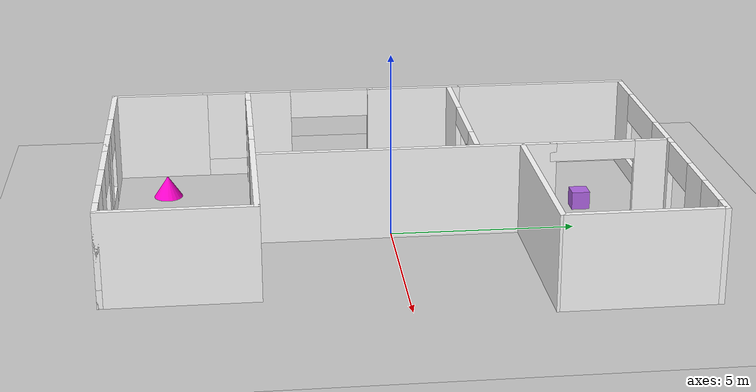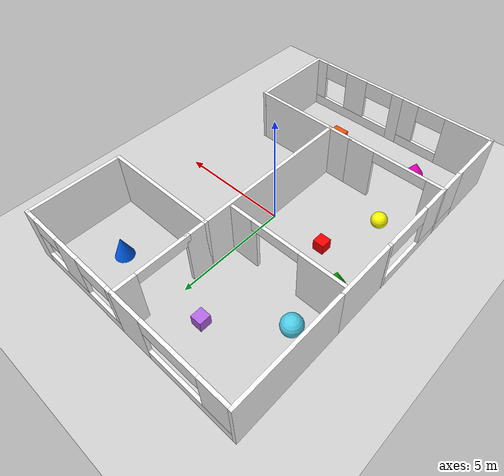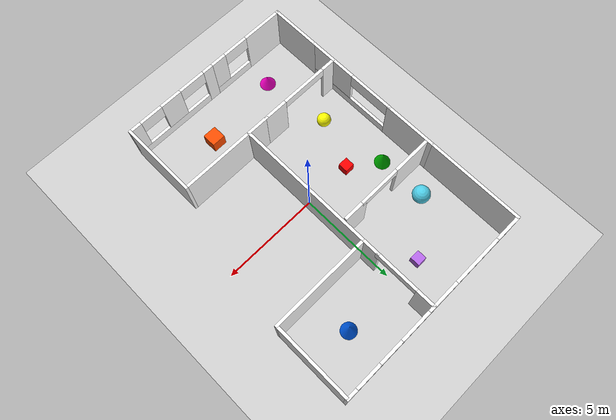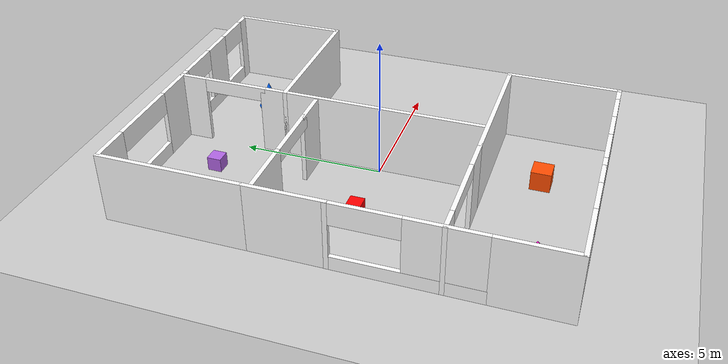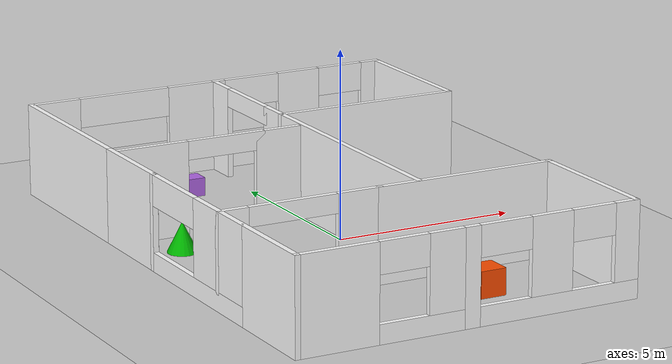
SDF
<?xml version="1.0" ?>
<sdf version='1.6'>
  <world name='custom_world'>

    <scene>
      <shadows>0</shadows>
    </scene>

    <gui fullscreen='0'>
      <camera name='user_camera'>
        <pose frame=''>0.319654 -0.235002 9.29441 0 1.5138 0.009599</pose>
        <view_controller>orbit</view_controller>
        <projection_type>perspective</projection_type>
      </camera>
    </gui>

    <physics type="ode">
      <real_time_update_rate>1000.0</real_time_update_rate>
      <max_step_size>0.001</max_step_size>
      <real_time_factor>1</real_time_factor>
      <ode>
        <solver>
          <type>quick</type>
          <iters>150</iters>
          <precon_iters>0</precon_iters>
          <sor>1.400000</sor>
          <use_dynamic_moi_rescaling>1</use_dynamic_moi_rescaling>
        </solver>
        <constraints>
          <cfm>0.00001</cfm>
          <erp>0.2</erp>
          <contact_max_correcting_vel>2000.000000</contact_max_correcting_vel>
          <contact_surface_layer>0.01000</contact_surface_layer>
        </constraints>
      </ode>
    </physics>

    <plugin name='gz::sim::systems::Physics' filename='gz-sim-physics-system'/>
    <plugin name='gz::sim::systems::UserCommands' filename='gz-sim-user-commands-system'/>
    <plugin name='gz::sim::systems::SceneBroadcaster' filename='gz-sim-scene-broadcaster-system'/>
    <plugin name='gz::sim::systems::Contact' filename='gz-sim-contact-system'/>
    <plugin name='gz::sim::systems::Sensors' filename='gz-sim-sensors-system'/>
    <plugin name='gz::sim::systems::Imu' filename='gz-sim-imu-system'/>

    <include>
      <uri>https://fuel.gazebosim.org/1.0/OpenRobotics/models/Ground Plane</uri>
    </include>

    <include>
      <uri>https://fuel.gazebosim.org/1.0/OpenRobotics/models/Sun</uri>
    </include>

    <model name='world_model'>
      <pose frame=''>0 0 0 0 0 1.5708</pose>

      <link name='wall_1'>
        <pose frame=''>5.07752 5.2688 0 0 -0 3.14159</pose>
        <self_collide>0</self_collide>
        <kinematic>0</kinematic>
        <visual name='wall_1_visual'>
          <pose frame=''>0 0 1.25 0 -0 0</pose>
          <geometry>
            <box>
              <size>5 0.15 2.5</size>
            </box>
          </geometry>
          <material>
            <pbr>
              <metal>
                <albedo_map>textures/bricks.png</albedo_map>
              </metal>
            </pbr>
            <ambient>1 1 1 1</ambient>
            <diffuse>1 1 1 1</diffuse>
            <specular>0.2 0.2 0.2 1</specular>
            <emissive>0 0 0 1</emissive>
          </material>
          <cast_shadows>1</cast_shadows>
          <transparency>0</transparency>
        </visual>
        <collision name='wall_1_collision'>
          <laser_retro>0</laser_retro>
          <max_contacts>10</max_contacts>
          <pose frame=''>0 0 1.25 0 -0 0</pose>
          <geometry>
            <box>
              <size>5 0.15 2.5</size>
            </box>
          </geometry>
          <surface>
            <friction>
              <ode>
                <mu>1</mu>
                <mu2>1</mu2>
                <fdir1>0 0 0</fdir1>
                <slip1>0</slip1>
                <slip2>0</slip2>
              </ode>
              <torsional>
                <coefficient>1</coefficient>
                <patch_radius>0</patch_radius>
                <surface_radius>0</surface_radius>
                <use_patch_radius>1</use_patch_radius>
                <ode>
                  <slip>0</slip>
                </ode>
              </torsional>
            </friction>
            <bounce>
              <restitution_coefficient>0</restitution_coefficient>
              <threshold>1e+06</threshold>
            </bounce>
            <contact>
              <collide_without_contact>0</collide_without_contact>
              <collide_without_contact_bitmask>1</collide_without_contact_bitmask>
              <collide_bitmask>1</collide_bitmask>
              <ode>
                <soft_cfm>0</soft_cfm>
                <soft_erp>0.2</soft_erp>
                <kp>1e+13</kp>
                <kd>1</kd>
                <max_vel>0.01</max_vel>
                <min_depth>0</min_depth>
              </ode>
              <bullet>
                <split_impulse>1</split_impulse>
                <split_impulse_penetration_threshold>-0.01</split_impulse_penetration_threshold>
                <soft_cfm>0</soft_cfm>
                <soft_erp>0.2</soft_erp>
                <kp>1e+13</kp>
                <kd>1</kd>
              </bullet>
            </contact>
          </surface>
        </collision>
      </link>

      <link name='wall_2'>
        <pose frame=''>1.25 5.26876 0 0 -0 3.14159</pose>
        <self_collide>0</self_collide>
        <kinematic>0</kinematic>
        <visual name='wall_2_visual'>
          <pose frame=''>0 0 1.25 0 -0 0</pose>
          <geometry>
            <box>
              <size>2.75 0.15 2.5</size>
            </box>
          </geometry>
          <material>
            <pbr>
              <metal>
                <albedo_map>textures/bricks.png</albedo_map>
              </metal>
            </pbr>
            <ambient>1 1 1 1</ambient>
            <diffuse>1 1 1 1</diffuse>
            <specular>0.2 0.2 0.2 1</specular>
            <emissive>0 0 0 1</emissive>
          </material>
          <cast_shadows>1</cast_shadows>
          <transparency>0</transparency>
        </visual>
        <collision name='wall_2_collision'>
          <laser_retro>0</laser_retro>
          <max_contacts>10</max_contacts>
          <pose frame=''>0 0 1.25 0 -0 0</pose>
          <geometry>
            <box>
              <size>2.75 0.15 2.5</size>
            </box>
          </geometry>
          <surface>
            <friction>
              <ode>
                <mu>1</mu>
                <mu2>1</mu2>
                <fdir1>0 0 0</fdir1>
                <slip1>0</slip1>
                <slip2>0</slip2>
              </ode>
              <torsional>
                <coefficient>1</coefficient>
                <patch_radius>0</patch_radius>
                <surface_radius>0</surface_radius>
                <use_patch_radius>1</use_patch_radius>
                <ode>
                  <slip>0</slip>
                </ode>
              </torsional>
            </friction>
            <bounce>
              <restitution_coefficient>0</restitution_coefficient>
              <threshold>1e+06</threshold>
            </bounce>
            <contact>
              <collide_without_contact>0</collide_without_contact>
              <collide_without_contact_bitmask>1</collide_without_contact_bitmask>
              <collide_bitmask>1</collide_bitmask>
              <ode>
                <soft_cfm>0</soft_cfm>
                <soft_erp>0.2</soft_erp>
                <kp>1e+13</kp>
                <kd>1</kd>
                <max_vel>0.01</max_vel>
                <min_depth>0</min_depth>
              </ode>
              <bullet>
                <split_impulse>1</split_impulse>
                <split_impulse_penetration_threshold>-0.01</split_impulse_penetration_threshold>
                <soft_cfm>0</soft_cfm>
                <soft_erp>0.2</soft_erp>
                <kp>1e+13</kp>
                <kd>1</kd>
              </bullet>
            </contact>
          </surface>
        </collision>
      </link>

      <link name='wall_3'>
        <pose frame=''>-2.475 5.275 0 0 -0 3.14159</pose>
        <self_collide>0</self_collide>
        <kinematic>0</kinematic>
        <visual name='wall_3_visual_1'>
          <pose frame=''>-2.41901 0 1.25 0 -0 0</pose>
          <geometry>
            <box>
              <size>0.161986 0.15 2.5</size>
            </box>
          </geometry>
          <material>
            <pbr>
              <metal>
                <albedo_map>textures/bricks.png</albedo_map>
              </metal>
            </pbr>
            <ambient>1 1 1 1</ambient>
            <diffuse>1 1 1 1</diffuse>
            <specular>0.2 0.2 0.2 1</specular>
            <emissive>0 0 0 1</emissive>
          </material>
          <cast_shadows>1</cast_shadows>
          <transparency>0</transparency>
        </visual>
        <visual name='wall_3_visual_2'>
          <pose frame=''>0.080993 0 0.25 0 -0 0</pose>
          <geometry>
            <box>
              <size>4.83801 0.15 0.5</size>
            </box>
          </geometry>
          <material>
            <pbr>
              <metal>
                <albedo_map>textures/bricks.png</albedo_map>
              </metal>
            </pbr>
            <ambient>1 1 1 1</ambient>
            <diffuse>1 1 1 1</diffuse>
            <specular>0.2 0.2 0.2 1</specular>
            <emissive>0 0 0 1</emissive>
          </material>
          <cast_shadows>1</cast_shadows>
          <transparency>0</transparency>
        </visual>
        <visual name='wall_3_visual_3'>
          <pose frame=''>1.2 0 1.5 0 -0 0</pose>
          <geometry>
            <box>
              <size>2.57501 0.15 2</size>
            </box>
          </geometry>
          <material>
            <pbr>
              <metal>
                <albedo_map>textures/bricks.png</albedo_map>
              </metal>
            </pbr>
            <ambient>1 1 1 1</ambient>
            <diffuse>1 1 1 1</diffuse>
            <specular>0.2 0.2 0.2 1</specular>
            <emissive>0 0 0 1</emissive>
          </material>
          <cast_shadows>1</cast_shadows>
          <transparency>0</transparency>
        </visual>
        <visual name='wall_3_visual_4'>
          <pose frame=''>-1.20651 0 2.1 0 -0 0</pose>
          <geometry>
            <box>
              <size>2.263 0.15 0.8</size>
            </box>
          </geometry>
          <material>
            <pbr>
              <metal>
                <albedo_map>textures/bricks.png</albedo_map>
              </metal>
            </pbr>
            <ambient>1 1 1 1</ambient>
            <diffuse>1 1 1 1</diffuse>
            <specular>0.2 0.2 0.2 1</specular>
            <emissive>0 0 0 1</emissive>
          </material>
          <cast_shadows>1</cast_shadows>
          <transparency>0</transparency>
        </visual>
        <collision name='wall_3_collision_1'>
          <laser_retro>0</laser_retro>
          <max_contacts>10</max_contacts>
          <pose frame=''>-2.41901 0 1.25 0 -0 0</pose>
          <geometry>
            <box>
              <size>0.161986 0.15 2.5</size>
            </box>
          </geometry>
          <surface>
            <friction>
              <ode>
                <mu>1</mu>
                <mu2>1</mu2>
                <fdir1>0 0 0</fdir1>
                <slip1>0</slip1>
                <slip2>0</slip2>
              </ode>
              <torsional>
                <coefficient>1</coefficient>
                <patch_radius>0</patch_radius>
                <surface_radius>0</surface_radius>
                <use_patch_radius>1</use_patch_radius>
                <ode>
                  <slip>0</slip>
                </ode>
              </torsional>
            </friction>
            <bounce>
              <restitution_coefficient>0</restitution_coefficient>
              <threshold>1e+06</threshold>
            </bounce>
            <contact>
              <collide_without_contact>0</collide_without_contact>
              <collide_without_contact_bitmask>1</collide_without_contact_bitmask>
              <collide_bitmask>1</collide_bitmask>
              <ode>
                <soft_cfm>0</soft_cfm>
                <soft_erp>0.2</soft_erp>
                <kp>1e+13</kp>
                <kd>1</kd>
                <max_vel>0.01</max_vel>
                <min_depth>0</min_depth>
              </ode>
              <bullet>
                <split_impulse>1</split_impulse>
                <split_impulse_penetration_threshold>-0.01</split_impulse_penetration_threshold>
                <soft_cfm>0</soft_cfm>
                <soft_erp>0.2</soft_erp>
                <kp>1e+13</kp>
                <kd>1</kd>
              </bullet>
            </contact>
          </surface>
        </collision>
        <collision name='wall_3_collision_2'>
          <laser_retro>0</laser_retro>
          <max_contacts>10</max_contacts>
          <pose frame=''>0.080993 0 0.25 0 -0 0</pose>
          <geometry>
            <box>
              <size>4.83801 0.15 0.5</size>
            </box>
          </geometry>
          <surface>
            <friction>
              <ode>
                <mu>1</mu>
                <mu2>1</mu2>
                <fdir1>0 0 0</fdir1>
                <slip1>0</slip1>
                <slip2>0</slip2>
              </ode>
              <torsional>
                <coefficient>1</coefficient>
                <patch_radius>0</patch_radius>
                <surface_radius>0</surface_radius>
                <use_patch_radius>1</use_patch_radius>
                <ode>
                  <slip>0</slip>
                </ode>
              </torsional>
            </friction>
            <bounce>
              <restitution_coefficient>0</restitution_coefficient>
              <threshold>1e+06</threshold>
            </bounce>
            <contact>
              <collide_without_contact>0</collide_without_contact>
              <collide_without_contact_bitmask>1</collide_without_contact_bitmask>
              <collide_bitmask>1</collide_bitmask>
              <ode>
                <soft_cfm>0</soft_cfm>
                <soft_erp>0.2</soft_erp>
                <kp>1e+13</kp>
                <kd>1</kd>
                <max_vel>0.01</max_vel>
                <min_depth>0</min_depth>
              </ode>
              <bullet>
                <split_impulse>1</split_impulse>
                <split_impulse_penetration_threshold>-0.01</split_impulse_penetration_threshold>
                <soft_cfm>0</soft_cfm>
                <soft_erp>0.2</soft_erp>
                <kp>1e+13</kp>
                <kd>1</kd>
              </bullet>
            </contact>
          </surface>
        </collision>
        <collision name='wall_3_collision_3'>
          <laser_retro>0</laser_retro>
          <max_contacts>10</max_contacts>
          <pose frame=''>1.2 0 1.5 0 -0 0</pose>
          <geometry>
            <box>
              <size>2.57501 0.15 2</size>
            </box>
          </geometry>
          <surface>
            <friction>
              <ode>
                <mu>1</mu>
                <mu2>1</mu2>
                <fdir1>0 0 0</fdir1>
                <slip1>0</slip1>
                <slip2>0</slip2>
              </ode>
              <torsional>
                <coefficient>1</coefficient>
                <patch_radius>0</patch_radius>
                <surface_radius>0</surface_radius>
                <use_patch_radius>1</use_patch_radius>
                <ode>
                  <slip>0</slip>
                </ode>
              </torsional>
            </friction>
            <bounce>
              <restitution_coefficient>0</restitution_coefficient>
              <threshold>1e+06</threshold>
            </bounce>
            <contact>
              <collide_without_contact>0</collide_without_contact>
              <collide_without_contact_bitmask>1</collide_without_contact_bitmask>
              <collide_bitmask>1</collide_bitmask>
              <ode>
                <soft_cfm>0</soft_cfm>
                <soft_erp>0.2</soft_erp>
                <kp>1e+13</kp>
                <kd>1</kd>
                <max_vel>0.01</max_vel>
                <min_depth>0</min_depth>
              </ode>
              <bullet>
                <split_impulse>1</split_impulse>
                <split_impulse_penetration_threshold>-0.01</split_impulse_penetration_threshold>
                <soft_cfm>0</soft_cfm>
                <soft_erp>0.2</soft_erp>
                <kp>1e+13</kp>
                <kd>1</kd>
              </bullet>
            </contact>
          </surface>
        </collision>
        <collision name='wall_3_collision_4'>
          <laser_retro>0</laser_retro>
          <max_contacts>10</max_contacts>
          <pose frame=''>-1.20651 0 2.1 0 -0 0</pose>
          <geometry>
            <box>
              <size>2.263 0.15 0.8</size>
            </box>
          </geometry>
          <surface>
            <friction>
              <ode>
                <mu>1</mu>
                <mu2>1</mu2>
                <fdir1>0 0 0</fdir1>
                <slip1>0</slip1>
                <slip2>0</slip2>
              </ode>
              <torsional>
                <coefficient>1</coefficient>
                <patch_radius>0</patch_radius>
                <surface_radius>0</surface_radius>
                <use_patch_radius>1</use_patch_radius>
                <ode>
                  <slip>0</slip>
                </ode>
              </torsional>
            </friction>
            <bounce>
              <restitution_coefficient>0</restitution_coefficient>
              <threshold>1e+06</threshold>
            </bounce>
            <contact>
              <collide_without_contact>0</collide_without_contact>
              <collide_without_contact_bitmask>1</collide_without_contact_bitmask>
              <collide_bitmask>1</collide_bitmask>
              <ode>
                <soft_cfm>0</soft_cfm>
                <soft_erp>0.2</soft_erp>
                <kp>1e+13</kp>
                <kd>1</kd>
                <max_vel>0.01</max_vel>
                <min_depth>0</min_depth>
              </ode>
              <bullet>
                <split_impulse>1</split_impulse>
                <split_impulse_penetration_threshold>-0.01</split_impulse_penetration_threshold>
                <soft_cfm>0</soft_cfm>
                <soft_erp>0.2</soft_erp>
                <kp>1e+13</kp>
                <kd>1</kd>
              </bullet>
            </contact>
          </surface>
        </collision>
      </link>

      <link name='wall_4'>
        <pose frame=''>-6.2 5.275 0 0 -0 3.14159</pose>
        <self_collide>0</self_collide>
        <kinematic>0</kinematic>
        <visual name='wall_4_visual'>
          <pose frame=''>0 0 1.25 0 -0 0</pose>
          <geometry>
            <box>
              <size>2.75 0.15 2.5</size>
            </box>
          </geometry>
          <material>
            <pbr>
              <metal>
                <albedo_map>textures/bricks.png</albedo_map>
              </metal>
            </pbr>
            <ambient>1 1 1 1</ambient>
            <diffuse>1 1 1 1</diffuse>
            <specular>0.2 0.2 0.2 1</specular>
            <emissive>0 0 0 1</emissive>
          </material>
          <cast_shadows>1</cast_shadows>
          <transparency>0</transparency>
        </visual>
        <collision name='wall_4_collision'>
          <laser_retro>0</laser_retro>
          <max_contacts>10</max_contacts>
          <pose frame=''>0 0 1.25 0 -0 0</pose>
          <geometry>
            <box>
              <size>2.75 0.15 2.5</size>
            </box>
          </geometry>
          <surface>
            <friction>
              <ode>
                <mu>1</mu>
                <mu2>1</mu2>
                <fdir1>0 0 0</fdir1>
                <slip1>0</slip1>
                <slip2>0</slip2>
              </ode>
              <torsional>
                <coefficient>1</coefficient>
                <patch_radius>0</patch_radius>
                <surface_radius>0</surface_radius>
                <use_patch_radius>1</use_patch_radius>
                <ode>
                  <slip>0</slip>
                </ode>
              </torsional>
            </friction>
            <bounce>
              <restitution_coefficient>0</restitution_coefficient>
              <threshold>1e+06</threshold>
            </bounce>
            <contact>
              <collide_without_contact>0</collide_without_contact>
              <collide_without_contact_bitmask>1</collide_without_contact_bitmask>
              <collide_bitmask>1</collide_bitmask>
              <ode>
                <soft_cfm>0</soft_cfm>
                <soft_erp>0.2</soft_erp>
                <kp>1e+13</kp>
                <kd>1</kd>
                <max_vel>0.01</max_vel>
                <min_depth>0</min_depth>
              </ode>
              <bullet>
                <split_impulse>1</split_impulse>
                <split_impulse_penetration_threshold>-0.01</split_impulse_penetration_threshold>
                <soft_cfm>0</soft_cfm>
                <soft_erp>0.2</soft_erp>
                <kp>1e+13</kp>
                <kd>1</kd>
              </bullet>
            </contact>
          </surface>
        </collision>
      </link>

      <link name='wall_5'>
        <pose frame=''>-7.5 3.1 0 0 0 -1.5708</pose>
        <self_collide>0</self_collide>
        <kinematic>0</kinematic>
        <visual name='wall_5_visual_1'>
          <pose frame=''>-1.14694 0 1.25 0 -0 0</pose>
          <geometry>
            <box>
              <size>2.20612 0.15 2.5</size>
            </box>
          </geometry>
          <material>
            <pbr>
              <metal>
                <albedo_map>textures/bricks.png</albedo_map>
              </metal>
            </pbr>
            <ambient>1 1 1 1</ambient>
            <diffuse>1 1 1 1</diffuse>
            <specular>0.2 0.2 0.2 1</specular>
            <emissive>0 0 0 1</emissive>
          </material>
          <cast_shadows>1</cast_shadows>
          <transparency>0</transparency>
        </visual>
        <visual name='wall_5_visual_2'>
          <pose frame=''>1.10306 0 0.25 0 -0 0</pose>
          <geometry>
            <box>
              <size>2.29388 0.15 0.5</size>
            </box>
          </geometry>
          <material>
            <pbr>
              <metal>
                <albedo_map>textures/bricks.png</albedo_map>
              </metal>
            </pbr>
            <ambient>1 1 1 1</ambient>
            <diffuse>1 1 1 1</diffuse>
            <specular>0.2 0.2 0.2 1</specular>
            <emissive>0 0 0 1</emissive>
          </material>
          <cast_shadows>1</cast_shadows>
          <transparency>0</transparency>
        </visual>
        <visual name='wall_5_visual_3'>
          <pose frame=''>1.76906 0 1.5 0 -0 0</pose>
          <geometry>
            <box>
              <size>0.96188 0.15 2</size>
            </box>
          </geometry>
          <material>
            <pbr>
              <metal>
                <albedo_map>textures/bricks.png</albedo_map>
              </metal>
            </pbr>
            <ambient>1 1 1 1</ambient>
            <diffuse>1 1 1 1</diffuse>
            <specular>0.2 0.2 0.2 1</specular>
            <emissive>0 0 0 1</emissive>
          </material>
          <cast_shadows>1</cast_shadows>
          <transparency>0</transparency>
        </visual>
        <visual name='wall_5_visual_4'>
          <pose frame=''>0.62212 0 2.1 0 -0 0</pose>
          <geometry>
            <box>
              <size>1.332 0.15 0.8</size>
            </box>
          </geometry>
          <material>
            <pbr>
              <metal>
                <albedo_map>textures/bricks.png</albedo_map>
              </metal>
            </pbr>
            <ambient>1 1 1 1</ambient>
            <diffuse>1 1 1 1</diffuse>
            <specular>0.2 0.2 0.2 1</specular>
            <emissive>0 0 0 1</emissive>
          </material>
          <cast_shadows>1</cast_shadows>
          <transparency>0</transparency>
        </visual>
        <collision name='wall_5_collision_1'>
          <laser_retro>0</laser_retro>
          <max_contacts>10</max_contacts>
          <pose frame=''>-1.14694 0 1.25 0 -0 0</pose>
          <geometry>
            <box>
              <size>2.20612 0.15 2.5</size>
            </box>
          </geometry>
          <surface>
            <friction>
              <ode>
                <mu>1</mu>
                <mu2>1</mu2>
                <fdir1>0 0 0</fdir1>
                <slip1>0</slip1>
                <slip2>0</slip2>
              </ode>
              <torsional>
                <coefficient>1</coefficient>
                <patch_radius>0</patch_radius>
                <surface_radius>0</surface_radius>
                <use_patch_radius>1</use_patch_radius>
                <ode>
                  <slip>0</slip>
                </ode>
              </torsional>
            </friction>
            <bounce>
              <restitution_coefficient>0</restitution_coefficient>
              <threshold>1e+06</threshold>
            </bounce>
            <contact>
              <collide_without_contact>0</collide_without_contact>
              <collide_without_contact_bitmask>1</collide_without_contact_bitmask>
              <collide_bitmask>1</collide_bitmask>
              <ode>
                <soft_cfm>0</soft_cfm>
                <soft_erp>0.2</soft_erp>
                <kp>1e+13</kp>
                <kd>1</kd>
                <max_vel>0.01</max_vel>
                <min_depth>0</min_depth>
              </ode>
              <bullet>
                <split_impulse>1</split_impulse>
                <split_impulse_penetration_threshold>-0.01</split_impulse_penetration_threshold>
                <soft_cfm>0</soft_cfm>
                <soft_erp>0.2</soft_erp>
                <kp>1e+13</kp>
                <kd>1</kd>
              </bullet>
            </contact>
          </surface>
        </collision>
        <collision name='wall_5_collision_2'>
          <laser_retro>0</laser_retro>
          <max_contacts>10</max_contacts>
          <pose frame=''>1.10306 0 0.25 0 -0 0</pose>
          <geometry>
            <box>
              <size>2.29388 0.15 0.5</size>
            </box>
          </geometry>
          <surface>
            <friction>
              <ode>
                <mu>1</mu>
                <mu2>1</mu2>
                <fdir1>0 0 0</fdir1>
                <slip1>0</slip1>
                <slip2>0</slip2>
              </ode>
              <torsional>
                <coefficient>1</coefficient>
                <patch_radius>0</patch_radius>
                <surface_radius>0</surface_radius>
                <use_patch_radius>1</use_patch_radius>
                <ode>
                  <slip>0</slip>
                </ode>
              </torsional>
            </friction>
            <bounce>
              <restitution_coefficient>0</restitution_coefficient>
              <threshold>1e+06</threshold>
            </bounce>
            <contact>
              <collide_without_contact>0</collide_without_contact>
              <collide_without_contact_bitmask>1</collide_without_contact_bitmask>
              <collide_bitmask>1</collide_bitmask>
              <ode>
                <soft_cfm>0</soft_cfm>
                <soft_erp>0.2</soft_erp>
                <kp>1e+13</kp>
                <kd>1</kd>
                <max_vel>0.01</max_vel>
                <min_depth>0</min_depth>
              </ode>
              <bullet>
                <split_impulse>1</split_impulse>
                <split_impulse_penetration_threshold>-0.01</split_impulse_penetration_threshold>
                <soft_cfm>0</soft_cfm>
                <soft_erp>0.2</soft_erp>
                <kp>1e+13</kp>
                <kd>1</kd>
              </bullet>
            </contact>
          </surface>
        </collision>
        <collision name='wall_5_collision_3'>
          <laser_retro>0</laser_retro>
          <max_contacts>10</max_contacts>
          <pose frame=''>1.76906 0 1.5 0 -0 0</pose>
          <geometry>
            <box>
              <size>0.96188 0.15 2</size>
            </box>
          </geometry>
          <surface>
            <friction>
              <ode>
                <mu>1</mu>
                <mu2>1</mu2>
                <fdir1>0 0 0</fdir1>
                <slip1>0</slip1>
                <slip2>0</slip2>
              </ode>
              <torsional>
                <coefficient>1</coefficient>
                <patch_radius>0</patch_radius>
                <surface_radius>0</surface_radius>
                <use_patch_radius>1</use_patch_radius>
                <ode>
                  <slip>0</slip>
                </ode>
              </torsional>
            </friction>
            <bounce>
              <restitution_coefficient>0</restitution_coefficient>
              <threshold>1e+06</threshold>
            </bounce>
            <contact>
              <collide_without_contact>0</collide_without_contact>
              <collide_without_contact_bitmask>1</collide_without_contact_bitmask>
              <collide_bitmask>1</collide_bitmask>
              <ode>
                <soft_cfm>0</soft_cfm>
                <soft_erp>0.2</soft_erp>
                <kp>1e+13</kp>
                <kd>1</kd>
                <max_vel>0.01</max_vel>
                <min_depth>0</min_depth>
              </ode>
              <bullet>
                <split_impulse>1</split_impulse>
                <split_impulse_penetration_threshold>-0.01</split_impulse_penetration_threshold>
                <soft_cfm>0</soft_cfm>
                <soft_erp>0.2</soft_erp>
                <kp>1e+13</kp>
                <kd>1</kd>
              </bullet>
            </contact>
          </surface>
        </collision>
        <collision name='wall_5_collision_4'>
          <laser_retro>0</laser_retro>
          <max_contacts>10</max_contacts>
          <pose frame=''>0.62212 0 2.1 0 -0 0</pose>
          <geometry>
            <box>
              <size>1.332 0.15 0.8</size>
            </box>
          </geometry>
          <surface>
            <friction>
              <ode>
                <mu>1</mu>
                <mu2>1</mu2>
                <fdir1>0 0 0</fdir1>
                <slip1>0</slip1>
                <slip2>0</slip2>
              </ode>
              <torsional>
                <coefficient>1</coefficient>
                <patch_radius>0</patch_radius>
                <surface_radius>0</surface_radius>
                <use_patch_radius>1</use_patch_radius>
                <ode>
                  <slip>0</slip>
                </ode>
              </torsional>
            </friction>
            <bounce>
              <restitution_coefficient>0</restitution_coefficient>
              <threshold>1e+06</threshold>
            </bounce>
            <contact>
              <collide_without_contact>0</collide_without_contact>
              <collide_without_contact_bitmask>1</collide_without_contact_bitmask>
              <collide_bitmask>1</collide_bitmask>
              <ode>
                <soft_cfm>0</soft_cfm>
                <soft_erp>0.2</soft_erp>
                <kp>1e+13</kp>
                <kd>1</kd>
                <max_vel>0.01</max_vel>
                <min_depth>0</min_depth>
              </ode>
              <bullet>
                <split_impulse>1</split_impulse>
                <split_impulse_penetration_threshold>-0.01</split_impulse_penetration_threshold>
                <soft_cfm>0</soft_cfm>
                <soft_erp>0.2</soft_erp>
                <kp>1e+13</kp>
                <kd>1</kd>
              </bullet>
            </contact>
          </surface>
        </collision>
      </link>

      <link name='wall_6'>
        <pose frame=''>-7.5 -1.5 0 0 0 -1.5708</pose>
        <self_collide>0</self_collide>
        <kinematic>0</kinematic>
        <visual name='wall_6_visual_1'>
          <pose frame=''>-2.21538 0 1.25 0 -0 0</pose>
          <geometry>
            <box>
              <size>0.569241 0.15 2.5</size>
            </box>
          </geometry>
          <material>
            <pbr>
              <metal>
                <albedo_map>textures/bricks.png</albedo_map>
              </metal>
            </pbr>
            <ambient>1 1 1 1</ambient>
            <diffuse>1 1 1 1</diffuse>
            <specular>0.2 0.2 0.2 1</specular>
            <emissive>0 0 0 1</emissive>
          </material>
          <cast_shadows>1</cast_shadows>
          <transparency>0</transparency>
        </visual>
        <visual name='wall_6_visual_2'>
          <pose frame=''>0.28462 0 0.25 0 -0 0</pose>
          <geometry>
            <box>
              <size>4.43076 0.15 0.5</size>
            </box>
          </geometry>
          <material>
            <pbr>
              <metal>
                <albedo_map>textures/bricks.png</albedo_map>
              </metal>
            </pbr>
            <ambient>1 1 1 1</ambient>
            <diffuse>1 1 1 1</diffuse>
            <specular>0.2 0.2 0.2 1</specular>
            <emissive>0 0 0 1</emissive>
          </material>
          <cast_shadows>1</cast_shadows>
          <transparency>0</transparency>
        </visual>
        <visual name='wall_6_visual_3'>
          <pose frame=''>0.0521 0 1.5 0 -0 0</pose>
          <geometry>
            <box>
              <size>1.14172 0.15 2</size>
            </box>
          </geometry>
          <material>
            <pbr>
              <metal>
                <albedo_map>textures/bricks.png</albedo_map>
              </metal>
            </pbr>
            <ambient>1 1 1 1</ambient>
            <diffuse>1 1 1 1</diffuse>
            <specular>0.2 0.2 0.2 1</specular>
            <emissive>0 0 0 1</emissive>
          </material>
          <cast_shadows>1</cast_shadows>
          <transparency>0</transparency>
        </visual>
        <visual name='wall_6_visual_4'>
          <pose frame=''>2.16098 0 1.5 0 -0 0</pose>
          <geometry>
            <box>
              <size>0.678041 0.15 2</size>
            </box>
          </geometry>
          <material>
            <pbr>
              <metal>
                <albedo_map>textures/bricks.png</albedo_map>
              </metal>
            </pbr>
            <ambient>1 1 1 1</ambient>
            <diffuse>1 1 1 1</diffuse>
            <specular>0.2 0.2 0.2 1</specular>
            <emissive>0 0 0 1</emissive>
          </material>
          <cast_shadows>1</cast_shadows>
          <transparency>0</transparency>
        </visual>
        <visual name='wall_6_visual_5'>
          <pose frame=''>-1.22476 0 2.1 0 -0 0</pose>
          <geometry>
            <box>
              <size>1.412 0.15 0.8</size>
            </box>
          </geometry>
          <material>
            <pbr>
              <metal>
                <albedo_map>textures/bricks.png</albedo_map>
              </metal>
            </pbr>
            <ambient>1 1 1 1</ambient>
            <diffuse>1 1 1 1</diffuse>
            <specular>0.2 0.2 0.2 1</specular>
            <emissive>0 0 0 1</emissive>
          </material>
          <cast_shadows>1</cast_shadows>
          <transparency>0</transparency>
        </visual>
        <visual name='wall_6_visual_6'>
          <pose frame=''>1.22246 0 2.1 0 -0 0</pose>
          <geometry>
            <box>
              <size>1.199 0.15 0.8</size>
            </box>
          </geometry>
          <material>
            <pbr>
              <metal>
                <albedo_map>textures/bricks.png</albedo_map>
              </metal>
            </pbr>
            <ambient>1 1 1 1</ambient>
            <diffuse>1 1 1 1</diffuse>
            <specular>0.2 0.2 0.2 1</specular>
            <emissive>0 0 0 1</emissive>
          </material>
          <cast_shadows>1</cast_shadows>
          <transparency>0</transparency>
        </visual>
        <collision name='wall_6_collision_1'>
          <laser_retro>0</laser_retro>
          <max_contacts>10</max_contacts>
          <pose frame=''>-2.21538 0 1.25 0 -0 0</pose>
          <geometry>
            <box>
              <size>0.569241 0.15 2.5</size>
            </box>
          </geometry>
          <surface>
            <friction>
              <ode>
                <mu>1</mu>
                <mu2>1</mu2>
                <fdir1>0 0 0</fdir1>
                <slip1>0</slip1>
                <slip2>0</slip2>
              </ode>
              <torsional>
                <coefficient>1</coefficient>
                <patch_radius>0</patch_radius>
                <surface_radius>0</surface_radius>
                <use_patch_radius>1</use_patch_radius>
                <ode>
                  <slip>0</slip>
                </ode>
              </torsional>
            </friction>
            <bounce>
              <restitution_coefficient>0</restitution_coefficient>
              <threshold>1e+06</threshold>
            </bounce>
            <contact>
              <collide_without_contact>0</collide_without_contact>
              <collide_without_contact_bitmask>1</collide_without_contact_bitmask>
              <collide_bitmask>1</collide_bitmask>
              <ode>
                <soft_cfm>0</soft_cfm>
                <soft_erp>0.2</soft_erp>
                <kp>1e+13</kp>
                <kd>1</kd>
                <max_vel>0.01</max_vel>
                <min_depth>0</min_depth>
              </ode>
              <bullet>
                <split_impulse>1</split_impulse>
                <split_impulse_penetration_threshold>-0.01</split_impulse_penetration_threshold>
                <soft_cfm>0</soft_cfm>
                <soft_erp>0.2</soft_erp>
                <kp>1e+13</kp>
                <kd>1</kd>
              </bullet>
            </contact>
          </surface>
        </collision>
        <collision name='wall_6_collision_2'>
          <laser_retro>0</laser_retro>
          <max_contacts>10</max_contacts>
          <pose frame=''>0.28462 0 0.25 0 -0 0</pose>
          <geometry>
            <box>
              <size>4.43076 0.15 0.5</size>
            </box>
          </geometry>
          <surface>
            <friction>
              <ode>
                <mu>1</mu>
                <mu2>1</mu2>
                <fdir1>0 0 0</fdir1>
                <slip1>0</slip1>
                <slip2>0</slip2>
              </ode>
              <torsional>
                <coefficient>1</coefficient>
                <patch_radius>0</patch_radius>
                <surface_radius>0</surface_radius>
                <use_patch_radius>1</use_patch_radius>
                <ode>
                  <slip>0</slip>
                </ode>
              </torsional>
            </friction>
            <bounce>
              <restitution_coefficient>0</restitution_coefficient>
              <threshold>1e+06</threshold>
            </bounce>
            <contact>
              <collide_without_contact>0</collide_without_contact>
              <collide_without_contact_bitmask>1</collide_without_contact_bitmask>
              <collide_bitmask>1</collide_bitmask>
              <ode>
                <soft_cfm>0</soft_cfm>
                <soft_erp>0.2</soft_erp>
                <kp>1e+13</kp>
                <kd>1</kd>
                <max_vel>0.01</max_vel>
                <min_depth>0</min_depth>
              </ode>
              <bullet>
                <split_impulse>1</split_impulse>
                <split_impulse_penetration_threshold>-0.01</split_impulse_penetration_threshold>
                <soft_cfm>0</soft_cfm>
                <soft_erp>0.2</soft_erp>
                <kp>1e+13</kp>
                <kd>1</kd>
              </bullet>
            </contact>
          </surface>
        </collision>
        <collision name='wall_6_collision_3'>
          <laser_retro>0</laser_retro>
          <max_contacts>10</max_contacts>
          <pose frame=''>0.0521 0 1.5 0 -0 0</pose>
          <geometry>
            <box>
              <size>1.14172 0.15 2</size>
            </box>
          </geometry>
          <surface>
            <friction>
              <ode>
                <mu>1</mu>
                <mu2>1</mu2>
                <fdir1>0 0 0</fdir1>
                <slip1>0</slip1>
                <slip2>0</slip2>
              </ode>
              <torsional>
                <coefficient>1</coefficient>
                <patch_radius>0</patch_radius>
                <surface_radius>0</surface_radius>
                <use_patch_radius>1</use_patch_radius>
                <ode>
                  <slip>0</slip>
                </ode>
              </torsional>
            </friction>
            <bounce>
              <restitution_coefficient>0</restitution_coefficient>
              <threshold>1e+06</threshold>
            </bounce>
            <contact>
              <collide_without_contact>0</collide_without_contact>
              <collide_without_contact_bitmask>1</collide_without_contact_bitmask>
              <collide_bitmask>1</collide_bitmask>
              <ode>
                <soft_cfm>0</soft_cfm>
                <soft_erp>0.2</soft_erp>
                <kp>1e+13</kp>
                <kd>1</kd>
                <max_vel>0.01</max_vel>
                <min_depth>0</min_depth>
              </ode>
              <bullet>
                <split_impulse>1</split_impulse>
                <split_impulse_penetration_threshold>-0.01</split_impulse_penetration_threshold>
                <soft_cfm>0</soft_cfm>
                <soft_erp>0.2</soft_erp>
                <kp>1e+13</kp>
                <kd>1</kd>
              </bullet>
            </contact>
          </surface>
        </collision>
        <collision name='wall_6_collision_4'>
          <laser_retro>0</laser_retro>
          <max_contacts>10</max_contacts>
          <pose frame=''>2.16098 0 1.5 0 -0 0</pose>
          <geometry>
            <box>
              <size>0.678041 0.15 2</size>
            </box>
          </geometry>
          <surface>
            <friction>
              <ode>
                <mu>1</mu>
                <mu2>1</mu2>
                <fdir1>0 0 0</fdir1>
                <slip1>0</slip1>
                <slip2>0</slip2>
              </ode>
              <torsional>
                <coefficient>1</coefficient>
                <patch_radius>0</patch_radius>
                <surface_radius>0</surface_radius>
                <use_patch_radius>1</use_patch_radius>
                <ode>
                  <slip>0</slip>
                </ode>
              </torsional>
            </friction>
            <bounce>
              <restitution_coefficient>0</restitution_coefficient>
              <threshold>1e+06</threshold>
            </bounce>
            <contact>
              <collide_without_contact>0</collide_without_contact>
              <collide_without_contact_bitmask>1</collide_without_contact_bitmask>
              <collide_bitmask>1</collide_bitmask>
              <ode>
                <soft_cfm>0</soft_cfm>
                <soft_erp>0.2</soft_erp>
                <kp>1e+13</kp>
                <kd>1</kd>
                <max_vel>0.01</max_vel>
                <min_depth>0</min_depth>
              </ode>
              <bullet>
                <split_impulse>1</split_impulse>
                <split_impulse_penetration_threshold>-0.01</split_impulse_penetration_threshold>
                <soft_cfm>0</soft_cfm>
                <soft_erp>0.2</soft_erp>
                <kp>1e+13</kp>
                <kd>1</kd>
              </bullet>
            </contact>
          </surface>
        </collision>
        <collision name='wall_6_collision_5'>
          <laser_retro>0</laser_retro>
          <max_contacts>10</max_contacts>
          <pose frame=''>-1.22476 0 2.1 0 -0 0</pose>
          <geometry>
            <box>
              <size>1.412 0.15 0.8</size>
            </box>
          </geometry>
          <surface>
            <friction>
              <ode>
                <mu>1</mu>
                <mu2>1</mu2>
                <fdir1>0 0 0</fdir1>
                <slip1>0</slip1>
                <slip2>0</slip2>
              </ode>
              <torsional>
                <coefficient>1</coefficient>
                <patch_radius>0</patch_radius>
                <surface_radius>0</surface_radius>
                <use_patch_radius>1</use_patch_radius>
                <ode>
                  <slip>0</slip>
                </ode>
              </torsional>
            </friction>
            <bounce>
              <restitution_coefficient>0</restitution_coefficient>
              <threshold>1e+06</threshold>
            </bounce>
            <contact>
              <collide_without_contact>0</collide_without_contact>
              <collide_without_contact_bitmask>1</collide_without_contact_bitmask>
              <collide_bitmask>1</collide_bitmask>
              <ode>
                <soft_cfm>0</soft_cfm>
                <soft_erp>0.2</soft_erp>
                <kp>1e+13</kp>
                <kd>1</kd>
                <max_vel>0.01</max_vel>
                <min_depth>0</min_depth>
              </ode>
              <bullet>
                <split_impulse>1</split_impulse>
                <split_impulse_penetration_threshold>-0.01</split_impulse_penetration_threshold>
                <soft_cfm>0</soft_cfm>
                <soft_erp>0.2</soft_erp>
                <kp>1e+13</kp>
                <kd>1</kd>
              </bullet>
            </contact>
          </surface>
        </collision>
        <collision name='wall_6_collision_6'>
          <laser_retro>0</laser_retro>
          <max_contacts>10</max_contacts>
          <pose frame=''>1.22246 0 2.1 0 -0 0</pose>
          <geometry>
            <box>
              <size>1.199 0.15 0.8</size>
            </box>
          </geometry>
          <surface>
            <friction>
              <ode>
                <mu>1</mu>
                <mu2>1</mu2>
                <fdir1>0 0 0</fdir1>
                <slip1>0</slip1>
                <slip2>0</slip2>
              </ode>
              <torsional>
                <coefficient>1</coefficient>
                <patch_radius>0</patch_radius>
                <surface_radius>0</surface_radius>
                <use_patch_radius>1</use_patch_radius>
                <ode>
                  <slip>0</slip>
                </ode>
              </torsional>
            </friction>
            <bounce>
              <restitution_coefficient>0</restitution_coefficient>
              <threshold>1e+06</threshold>
            </bounce>
            <contact>
              <collide_without_contact>0</collide_without_contact>
              <collide_without_contact_bitmask>1</collide_without_contact_bitmask>
              <collide_bitmask>1</collide_bitmask>
              <ode>
                <soft_cfm>0</soft_cfm>
                <soft_erp>0.2</soft_erp>
                <kp>1e+13</kp>
                <kd>1</kd>
                <max_vel>0.01</max_vel>
                <min_depth>0</min_depth>
              </ode>
              <bullet>
                <split_impulse>1</split_impulse>
                <split_impulse_penetration_threshold>-0.01</split_impulse_penetration_threshold>
                <soft_cfm>0</soft_cfm>
                <soft_erp>0.2</soft_erp>
                <kp>1e+13</kp>
                <kd>1</kd>
              </bullet>
            </contact>
          </surface>
        </collision>
      </link>

      <link name='wall_7'>
        <pose frame=''>-5.575 -3.925 0 0 -0 0</pose>
        <self_collide>0</self_collide>
        <kinematic>0</kinematic>
        <visual name='wall_7_visual'>
          <pose frame=''>0 0 1.25 0 -0 0</pose>
          <geometry>
            <box>
              <size>4 0.15 2.5</size>
            </box>
          </geometry>
          <material>
            <pbr>
              <metal>
                <albedo_map>textures/bricks.png</albedo_map>
              </metal>
            </pbr>
            <ambient>1 1 1 1</ambient>
            <diffuse>1 1 1 1</diffuse>
            <specular>0.2 0.2 0.2 1</specular>
            <emissive>0 0 0 1</emissive>
          </material>
          <cast_shadows>1</cast_shadows>
          <transparency>0</transparency>
        </visual>
        <collision name='wall_7_collision'>
          <laser_retro>0</laser_retro>
          <max_contacts>10</max_contacts>
          <pose frame=''>0 0 1.25 0 -0 0</pose>
          <geometry>
            <box>
              <size>4 0.15 2.5</size>
            </box>
          </geometry>
          <surface>
            <friction>
              <ode>
                <mu>1</mu>
                <mu2>1</mu2>
                <fdir1>0 0 0</fdir1>
                <slip1>0</slip1>
                <slip2>0</slip2>
              </ode>
              <torsional>
                <coefficient>1</coefficient>
                <patch_radius>0</patch_radius>
                <surface_radius>0</surface_radius>
                <use_patch_radius>1</use_patch_radius>
                <ode>
                  <slip>0</slip>
                </ode>
              </torsional>
            </friction>
            <bounce>
              <restitution_coefficient>0</restitution_coefficient>
              <threshold>1e+06</threshold>
            </bounce>
            <contact>
              <collide_without_contact>0</collide_without_contact>
              <collide_without_contact_bitmask>1</collide_without_contact_bitmask>
              <collide_bitmask>1</collide_bitmask>
              <ode>
                <soft_cfm>0</soft_cfm>
                <soft_erp>0.2</soft_erp>
                <kp>1e+13</kp>
                <kd>1</kd>
                <max_vel>0.01</max_vel>
                <min_depth>0</min_depth>
              </ode>
              <bullet>
                <split_impulse>1</split_impulse>
                <split_impulse_penetration_threshold>-0.01</split_impulse_penetration_threshold>
                <soft_cfm>0</soft_cfm>
                <soft_erp>0.2</soft_erp>
                <kp>1e+13</kp>
                <kd>1</kd>
              </bullet>
            </contact>
          </surface>
        </collision>
      </link>

      <link name='wall_8'>
        <pose frame=''>-3.65151 -1.49625 0 0 -0 1.5708</pose>
        <self_collide>0</self_collide>
        <kinematic>0</kinematic>
        <visual name='wall_8_visual'>
          <pose frame=''>0 0 1.25 0 -0 0</pose>
          <geometry>
            <box>
              <size>5 0.15 2.5</size>
            </box>
          </geometry>
          <material>
            <pbr>
              <metal>
                <albedo_map>textures/bricks.png</albedo_map>
              </metal>
            </pbr>
            <ambient>1 1 1 1</ambient>
            <diffuse>1 1 1 1</diffuse>
            <specular>0.2 0.2 0.2 1</specular>
            <emissive>0 0 0 1</emissive>
          </material>
          <cast_shadows>1</cast_shadows>
          <transparency>0</transparency>
        </visual>
        <collision name='wall_8_collision'>
          <laser_retro>0</laser_retro>
          <max_contacts>10</max_contacts>
          <pose frame=''>0 0 1.25 0 -0 0</pose>
          <geometry>
            <box>
              <size>5 0.15 2.5</size>
            </box>
          </geometry>
          <surface>
            <friction>
              <ode>
                <mu>1</mu>
                <mu2>1</mu2>
                <fdir1>0 0 0</fdir1>
                <slip1>0</slip1>
                <slip2>0</slip2>
              </ode>
              <torsional>
                <coefficient>1</coefficient>
                <patch_radius>0</patch_radius>
                <surface_radius>0</surface_radius>
                <use_patch_radius>1</use_patch_radius>
                <ode>
                  <slip>0</slip>
                </ode>
              </torsional>
            </friction>
            <bounce>
              <restitution_coefficient>0</restitution_coefficient>
              <threshold>1e+06</threshold>
            </bounce>
            <contact>
              <collide_without_contact>0</collide_without_contact>
              <collide_without_contact_bitmask>1</collide_without_contact_bitmask>
              <collide_bitmask>1</collide_bitmask>
              <ode>
                <soft_cfm>0</soft_cfm>
                <soft_erp>0.2</soft_erp>
                <kp>1e+13</kp>
                <kd>1</kd>
                <max_vel>0.01</max_vel>
                <min_depth>0</min_depth>
              </ode>
              <bullet>
                <split_impulse>1</split_impulse>
                <split_impulse_penetration_threshold>-0.01</split_impulse_penetration_threshold>
                <soft_cfm>0</soft_cfm>
                <soft_erp>0.2</soft_erp>
                <kp>1e+13</kp>
                <kd>1</kd>
              </bullet>
            </contact>
          </surface>
        </collision>
      </link>

      <link name='wall_9'>
        <pose frame=''>2.29994 2.5 0 0 0 -1.57091</pose>
        <self_collide>0</self_collide>
        <kinematic>0</kinematic>
        <visual name='wall_9_visual_1'>
          <pose frame=''>-1.7 0 1.25 0 -0 0</pose>
          <geometry>
            <box>
              <size>2 0.15 2.5</size>
            </box>
          </geometry>
          <material>
            <pbr>
              <metal>
                <albedo_map>textures/bricks.png</albedo_map>
              </metal>
            </pbr>
            <ambient>1 1 1 1</ambient>
            <diffuse>1 1 1 1</diffuse>
            <specular>0.2 0.2 0.2 1</specular>
            <emissive>0 0 0 1</emissive>
          </material>
          <cast_shadows>1</cast_shadows>
          <transparency>0</transparency>
        </visual>
        <visual name='wall_9_visual_2'>
          <pose frame=''>1.9 0 1.25 0 -0 0</pose>
          <geometry>
            <box>
              <size>1.3 0.15 2.5</size>
            </box>
          </geometry>
          <material>
            <pbr>
              <metal>
                <albedo_map>textures/bricks.png</albedo_map>
              </metal>
            </pbr>
            <ambient>1 1 1 1</ambient>
            <diffuse>1 1 1 1</diffuse>
            <specular>0.2 0.2 0.2 1</specular>
            <emissive>0 0 0 1</emissive>
          </material>
          <cast_shadows>1</cast_shadows>
          <transparency>0</transparency>
        </visual>
        <visual name='wall_9_visual_3'>
          <pose frame=''>0.4 0 2.25 0 -0 0</pose>
          <geometry>
            <box>
              <size>2.2 0.15 0.5</size>
            </box>
          </geometry>
          <material>
            <pbr>
              <metal>
                <albedo_map>textures/bricks.png</albedo_map>
              </metal>
            </pbr>
            <ambient>1 1 1 1</ambient>
            <diffuse>1 1 1 1</diffuse>
            <specular>0.2 0.2 0.2 1</specular>
            <emissive>0 0 0 1</emissive>
          </material>
          <cast_shadows>1</cast_shadows>
          <transparency>0</transparency>
        </visual>
        <collision name='wall_9_collision_1'>
          <laser_retro>0</laser_retro>
          <max_contacts>10</max_contacts>
          <pose frame=''>-1.7 0 1.25 0 -0 0</pose>
          <geometry>
            <box>
              <size>2 0.15 2.5</size>
            </box>
          </geometry>
          <surface>
            <friction>
              <ode>
                <mu>1</mu>
                <mu2>1</mu2>
                <fdir1>0 0 0</fdir1>
                <slip1>0</slip1>
                <slip2>0</slip2>
              </ode>
              <torsional>
                <coefficient>1</coefficient>
                <patch_radius>0</patch_radius>
                <surface_radius>0</surface_radius>
                <use_patch_radius>1</use_patch_radius>
                <ode>
                  <slip>0</slip>
                </ode>
              </torsional>
            </friction>
            <bounce>
              <restitution_coefficient>0</restitution_coefficient>
              <threshold>1e+06</threshold>
            </bounce>
            <contact>
              <collide_without_contact>0</collide_without_contact>
              <collide_without_contact_bitmask>1</collide_without_contact_bitmask>
              <collide_bitmask>1</collide_bitmask>
              <ode>
                <soft_cfm>0</soft_cfm>
                <soft_erp>0.2</soft_erp>
                <kp>1e+13</kp>
                <kd>1</kd>
                <max_vel>0.01</max_vel>
                <min_depth>0</min_depth>
              </ode>
              <bullet>
                <split_impulse>1</split_impulse>
                <split_impulse_penetration_threshold>-0.01</split_impulse_penetration_threshold>
                <soft_cfm>0</soft_cfm>
                <soft_erp>0.2</soft_erp>
                <kp>1e+13</kp>
                <kd>1</kd>
              </bullet>
            </contact>
          </surface>
        </collision>
        <collision name='wall_9_collision_2'>
          <laser_retro>0</laser_retro>
          <max_contacts>10</max_contacts>
          <pose frame=''>1.9 0 1.25 0 -0 0</pose>
          <geometry>
            <box>
              <size>1.3 0.15 2.5</size>
            </box>
          </geometry>
          <surface>
            <friction>
              <ode>
                <mu>1</mu>
                <mu2>1</mu2>
                <fdir1>0 0 0</fdir1>
                <slip1>0</slip1>
                <slip2>0</slip2>
              </ode>
              <torsional>
                <coefficient>1</coefficient>
                <patch_radius>0</patch_radius>
                <surface_radius>0</surface_radius>
                <use_patch_radius>1</use_patch_radius>
                <ode>
                  <slip>0</slip>
                </ode>
              </torsional>
            </friction>
            <bounce>
              <restitution_coefficient>0</restitution_coefficient>
              <threshold>1e+06</threshold>
            </bounce>
            <contact>
              <collide_without_contact>0</collide_without_contact>
              <collide_without_contact_bitmask>1</collide_without_contact_bitmask>
              <collide_bitmask>1</collide_bitmask>
              <ode>
                <soft_cfm>0</soft_cfm>
                <soft_erp>0.2</soft_erp>
                <kp>1e+13</kp>
                <kd>1</kd>
                <max_vel>0.01</max_vel>
                <min_depth>0</min_depth>
              </ode>
              <bullet>
                <split_impulse>1</split_impulse>
                <split_impulse_penetration_threshold>-0.01</split_impulse_penetration_threshold>
                <soft_cfm>0</soft_cfm>
                <soft_erp>0.2</soft_erp>
                <kp>1e+13</kp>
                <kd>1</kd>
              </bullet>
            </contact>
          </surface>
        </collision>
        <collision name='wall_9_collision_3'>
          <laser_retro>0</laser_retro>
          <max_contacts>10</max_contacts>
          <pose frame=''>0.4 0 2.25 0 -0 0</pose>
          <geometry>
            <box>
              <size>2.2 0.15 0.5</size>
            </box>
          </geometry>
          <surface>
            <friction>
              <ode>
                <mu>1</mu>
                <mu2>1</mu2>
                <fdir1>0 0 0</fdir1>
                <slip1>0</slip1>
                <slip2>0</slip2>
              </ode>
              <torsional>
                <coefficient>1</coefficient>
                <patch_radius>0</patch_radius>
                <surface_radius>0</surface_radius>
                <use_patch_radius>1</use_patch_radius>
                <ode>
                  <slip>0</slip>
                </ode>
              </torsional>
            </friction>
            <bounce>
              <restitution_coefficient>0</restitution_coefficient>
              <threshold>1e+06</threshold>
            </bounce>
            <contact>
              <collide_without_contact>0</collide_without_contact>
              <collide_without_contact_bitmask>1</collide_without_contact_bitmask>
              <collide_bitmask>1</collide_bitmask>
              <ode>
                <soft_cfm>0</soft_cfm>
                <soft_erp>0.2</soft_erp>
                <kp>1e+13</kp>
                <kd>1</kd>
                <max_vel>0.01</max_vel>
                <min_depth>0</min_depth>
              </ode>
              <bullet>
                <split_impulse>1</split_impulse>
                <split_impulse_penetration_threshold>-0.01</split_impulse_penetration_threshold>
                <soft_cfm>0</soft_cfm>
                <soft_erp>0.2</soft_erp>
                <kp>1e+13</kp>
                <kd>1</kd>
              </bullet>
            </contact>
          </surface>
        </collision>
      </link>

      <link name='wall_10'>
        <pose frame=''>-0.1 -0.17494 0 0 0 -4.6e-05</pose>
        <self_collide>0</self_collide>
        <kinematic>0</kinematic>
        <visual name='wall_10_visual'>
          <pose frame=''>0 0 1.25 0 -0 0</pose>
          <geometry>
            <box>
              <size>7.2 0.15 2.5</size>
            </box>
          </geometry>
          <material>
            <pbr>
              <metal>
                <albedo_map>textures/bricks.png</albedo_map>
              </metal>
            </pbr>
            <ambient>1 1 1 1</ambient>
            <diffuse>1 1 1 1</diffuse>
            <specular>0.2 0.2 0.2 1</specular>
            <emissive>0 0 0 1</emissive>
          </material>
          <cast_shadows>1</cast_shadows>
          <transparency>0</transparency>
        </visual>
        <collision name='wall_10_collision'>
          <laser_retro>0</laser_retro>
          <max_contacts>10</max_contacts>
          <pose frame=''>0 0 1.25 0 -0 0</pose>
          <geometry>
            <box>
              <size>7.2 0.15 2.5</size>
            </box>
          </geometry>
          <surface>
            <friction>
              <ode>
                <mu>1</mu>
                <mu2>1</mu2>
                <fdir1>0 0 0</fdir1>
                <slip1>0</slip1>
                <slip2>0</slip2>
              </ode>
              <torsional>
                <coefficient>1</coefficient>
                <patch_radius>0</patch_radius>
                <surface_radius>0</surface_radius>
                <use_patch_radius>1</use_patch_radius>
                <ode>
                  <slip>0</slip>
                </ode>
              </torsional>
            </friction>
            <bounce>
              <restitution_coefficient>0</restitution_coefficient>
              <threshold>1e+06</threshold>
            </bounce>
            <contact>
              <collide_without_contact>0</collide_without_contact>
              <collide_without_contact_bitmask>1</collide_without_contact_bitmask>
              <collide_bitmask>1</collide_bitmask>
              <ode>
                <soft_cfm>0</soft_cfm>
                <soft_erp>0.2</soft_erp>
                <kp>1e+13</kp>
                <kd>1</kd>
                <max_vel>0.01</max_vel>
                <min_depth>0</min_depth>
              </ode>
              <bullet>
                <split_impulse>1</split_impulse>
                <split_impulse_penetration_threshold>-0.01</split_impulse_penetration_threshold>
                <soft_cfm>0</soft_cfm>
                <soft_erp>0.2</soft_erp>
                <kp>1e+13</kp>
                <kd>1</kd>
              </bullet>
            </contact>
          </surface>
        </collision>
      </link>

      <link name='wall_11'>
        <pose frame=''>3.5 -2.725 0 0 0 -1.5708</pose>
        <self_collide>0</self_collide>
        <kinematic>0</kinematic>
        <visual name='wall_11_visual'>
          <pose frame=''>0 0 1.25 0 -0 0</pose>
          <geometry>
            <box>
              <size>5.25 0.15 2.5</size>
            </box>
          </geometry>
          <material>
            <pbr>
              <metal>
                <albedo_map>textures/bricks.png</albedo_map>
              </metal>
            </pbr>
            <ambient>1 1 1 1</ambient>
            <diffuse>1 1 1 1</diffuse>
            <specular>0.2 0.2 0.2 1</specular>
            <emissive>0 0 0 1</emissive>
          </material>
          <cast_shadows>1</cast_shadows>
          <transparency>0</transparency>
        </visual>
        <collision name='wall_11_collision'>
          <laser_retro>0</laser_retro>
          <max_contacts>10</max_contacts>
          <pose frame=''>0 0 1.25 0 -0 0</pose>
          <geometry>
            <box>
              <size>5.25 0.15 2.5</size>
            </box>
          </geometry>
          <surface>
            <friction>
              <ode>
                <mu>1</mu>
                <mu2>1</mu2>
                <fdir1>0 0 0</fdir1>
                <slip1>0</slip1>
                <slip2>0</slip2>
              </ode>
              <torsional>
                <coefficient>1</coefficient>
                <patch_radius>0</patch_radius>
                <surface_radius>0</surface_radius>
                <use_patch_radius>1</use_patch_radius>
                <ode>
                  <slip>0</slip>
                </ode>
              </torsional>
            </friction>
            <bounce>
              <restitution_coefficient>0</restitution_coefficient>
              <threshold>1e+06</threshold>
            </bounce>
            <contact>
              <collide_without_contact>0</collide_without_contact>
              <collide_without_contact_bitmask>1</collide_without_contact_bitmask>
              <collide_bitmask>1</collide_bitmask>
              <ode>
                <soft_cfm>0</soft_cfm>
                <soft_erp>0.2</soft_erp>
                <kp>1e+13</kp>
                <kd>1</kd>
                <max_vel>0.01</max_vel>
                <min_depth>0</min_depth>
              </ode>
              <bullet>
                <split_impulse>1</split_impulse>
                <split_impulse_penetration_threshold>-0.01</split_impulse_penetration_threshold>
                <soft_cfm>0</soft_cfm>
                <soft_erp>0.2</soft_erp>
                <kp>1e+13</kp>
                <kd>1</kd>
              </bullet>
            </contact>
          </surface>
        </collision>
      </link>

      <link name='wall_12'>
        <pose frame=''>5.5 -5.275 0 0 -0 0</pose>
        <self_collide>0</self_collide>
        <kinematic>0</kinematic>
        <visual name='wall_12_visual'>
          <pose frame=''>0 0 1.25 0 -0 0</pose>
          <geometry>
            <box>
              <size>4 0.15 2.5</size>
            </box>
          </geometry>
          <material>
            <pbr>
              <metal>
                <albedo_map>textures/bricks.png</albedo_map>
              </metal>
            </pbr>
            <ambient>1 1 1 1</ambient>
            <diffuse>1 1 1 1</diffuse>
            <specular>0.2 0.2 0.2 1</specular>
            <emissive>0 0 0 1</emissive>
          </material>
          <cast_shadows>1</cast_shadows>
          <transparency>0</transparency>
        </visual>
        <collision name='wall_12_collision'>
          <laser_retro>0</laser_retro>
          <max_contacts>10</max_contacts>
          <pose frame=''>0 0 1.25 0 -0 0</pose>
          <geometry>
            <box>
              <size>4 0.15 2.5</size>
            </box>
          </geometry>
          <surface>
            <friction>
              <ode>
                <mu>1</mu>
                <mu2>1</mu2>
                <fdir1>0 0 0</fdir1>
                <slip1>0</slip1>
                <slip2>0</slip2>
              </ode>
              <torsional>
                <coefficient>1</coefficient>
                <patch_radius>0</patch_radius>
                <surface_radius>0</surface_radius>
                <use_patch_radius>1</use_patch_radius>
                <ode>
                  <slip>0</slip>
                </ode>
              </torsional>
            </friction>
            <bounce>
              <restitution_coefficient>0</restitution_coefficient>
              <threshold>1e+06</threshold>
            </bounce>
            <contact>
              <collide_without_contact>0</collide_without_contact>
              <collide_without_contact_bitmask>1</collide_without_contact_bitmask>
              <collide_bitmask>1</collide_bitmask>
              <ode>
                <soft_cfm>0</soft_cfm>
                <soft_erp>0.2</soft_erp>
                <kp>1e+13</kp>
                <kd>1</kd>
                <max_vel>0.01</max_vel>
                <min_depth>0</min_depth>
              </ode>
              <bullet>
                <split_impulse>1</split_impulse>
                <split_impulse_penetration_threshold>-0.01</split_impulse_penetration_threshold>
                <soft_cfm>0</soft_cfm>
                <soft_erp>0.2</soft_erp>
                <kp>1e+13</kp>
                <kd>1</kd>
              </bullet>
            </contact>
          </surface>
        </collision>
      </link>

      <link name='wall_13'>
        <pose frame=''>7.5 -2.725 0 0 -0 1.5708</pose>
        <self_collide>0</self_collide>
        <kinematic>0</kinematic>
        <visual name='wall_13_visual_1'>
          <pose frame=''>-2.32929 0 1.25 0 -0 0</pose>
          <geometry>
            <box>
              <size>0.591431 0.15 2.5</size>
            </box>
          </geometry>
          <material>
            <pbr>
              <metal>
                <albedo_map>textures/bricks.png</albedo_map>
              </metal>
            </pbr>
            <ambient>1 1 1 1</ambient>
            <diffuse>1 1 1 1</diffuse>
            <specular>0.2 0.2 0.2 1</specular>
            <emissive>0 0 0 1</emissive>
          </material>
          <cast_shadows>1</cast_shadows>
          <transparency>0</transparency>
        </visual>
        <visual name='wall_13_visual_2'>
          <pose frame=''>0.295715 0 0.25 0 -0 0</pose>
          <geometry>
            <box>
              <size>4.65857 0.15 0.5</size>
            </box>
          </geometry>
          <material>
            <pbr>
              <metal>
                <albedo_map>textures/bricks.png</albedo_map>
              </metal>
            </pbr>
            <ambient>1 1 1 1</ambient>
            <diffuse>1 1 1 1</diffuse>
            <specular>0.2 0.2 0.2 1</specular>
            <emissive>0 0 0 1</emissive>
          </material>
          <cast_shadows>1</cast_shadows>
          <transparency>0</transparency>
        </visual>
        <visual name='wall_13_visual_3'>
          <pose frame=''>-0.036959 0 1.5 0 -0 0</pose>
          <geometry>
            <box>
              <size>1.27522 0.15 2</size>
            </box>
          </geometry>
          <material>
            <pbr>
              <metal>
                <albedo_map>textures/bricks.png</albedo_map>
              </metal>
            </pbr>
            <ambient>1 1 1 1</ambient>
            <diffuse>1 1 1 1</diffuse>
            <specular>0.2 0.2 0.2 1</specular>
            <emissive>0 0 0 1</emissive>
          </material>
          <cast_shadows>1</cast_shadows>
          <transparency>0</transparency>
        </visual>
        <visual name='wall_13_visual_4'>
          <pose frame=''>2.43783 0 1.5 0 -0 0</pose>
          <geometry>
            <box>
              <size>0.374348 0.15 2</size>
            </box>
          </geometry>
          <material>
            <pbr>
              <metal>
                <albedo_map>textures/bricks.png</albedo_map>
              </metal>
            </pbr>
            <ambient>1 1 1 1</ambient>
            <diffuse>1 1 1 1</diffuse>
            <specular>0.2 0.2 0.2 1</specular>
            <emissive>0 0 0 1</emissive>
          </material>
          <cast_shadows>1</cast_shadows>
          <transparency>0</transparency>
        </visual>
        <visual name='wall_13_visual_5'>
          <pose frame=''>-1.35407 0 2.1 0 -0 0</pose>
          <geometry>
            <box>
              <size>1.359 0.15 0.8</size>
            </box>
          </geometry>
          <material>
            <pbr>
              <metal>
                <albedo_map>textures/bricks.png</albedo_map>
              </metal>
            </pbr>
            <ambient>1 1 1 1</ambient>
            <diffuse>1 1 1 1</diffuse>
            <specular>0.2 0.2 0.2 1</specular>
            <emissive>0 0 0 1</emissive>
          </material>
          <cast_shadows>1</cast_shadows>
          <transparency>0</transparency>
        </visual>
        <visual name='wall_13_visual_6'>
          <pose frame=''>1.42565 0 2.1 0 -0 0</pose>
          <geometry>
            <box>
              <size>1.65 0.15 0.8</size>
            </box>
          </geometry>
          <material>
            <pbr>
              <metal>
                <albedo_map>textures/bricks.png</albedo_map>
              </metal>
            </pbr>
            <ambient>1 1 1 1</ambient>
            <diffuse>1 1 1 1</diffuse>
            <specular>0.2 0.2 0.2 1</specular>
            <emissive>0 0 0 1</emissive>
          </material>
          <cast_shadows>1</cast_shadows>
          <transparency>0</transparency>
        </visual>
        <collision name='wall_13_collision_1'>
          <laser_retro>0</laser_retro>
          <max_contacts>10</max_contacts>
          <pose frame=''>-2.32929 0 1.25 0 -0 0</pose>
          <geometry>
            <box>
              <size>0.591431 0.15 2.5</size>
            </box>
          </geometry>
          <surface>
            <friction>
              <ode>
                <mu>1</mu>
                <mu2>1</mu2>
                <fdir1>0 0 0</fdir1>
                <slip1>0</slip1>
                <slip2>0</slip2>
              </ode>
              <torsional>
                <coefficient>1</coefficient>
                <patch_radius>0</patch_radius>
                <surface_radius>0</surface_radius>
                <use_patch_radius>1</use_patch_radius>
                <ode>
                  <slip>0</slip>
                </ode>
              </torsional>
            </friction>
            <bounce>
              <restitution_coefficient>0</restitution_coefficient>
              <threshold>1e+06</threshold>
            </bounce>
            <contact>
              <collide_without_contact>0</collide_without_contact>
              <collide_without_contact_bitmask>1</collide_without_contact_bitmask>
              <collide_bitmask>1</collide_bitmask>
              <ode>
                <soft_cfm>0</soft_cfm>
                <soft_erp>0.2</soft_erp>
                <kp>1e+13</kp>
                <kd>1</kd>
                <max_vel>0.01</max_vel>
                <min_depth>0</min_depth>
              </ode>
              <bullet>
                <split_impulse>1</split_impulse>
                <split_impulse_penetration_threshold>-0.01</split_impulse_penetration_threshold>
                <soft_cfm>0</soft_cfm>
                <soft_erp>0.2</soft_erp>
                <kp>1e+13</kp>
                <kd>1</kd>
              </bullet>
            </contact>
          </surface>
        </collision>
        <collision name='wall_13_collision_2'>
          <laser_retro>0</laser_retro>
          <max_contacts>10</max_contacts>
          <pose frame=''>0.295715 0 0.25 0 -0 0</pose>
          <geometry>
            <box>
              <size>4.65857 0.15 0.5</size>
            </box>
          </geometry>
          <surface>
            <friction>
              <ode>
                <mu>1</mu>
                <mu2>1</mu2>
                <fdir1>0 0 0</fdir1>
                <slip1>0</slip1>
                <slip2>0</slip2>
              </ode>
              <torsional>
                <coefficient>1</coefficient>
                <patch_radius>0</patch_radius>
                <surface_radius>0</surface_radius>
                <use_patch_radius>1</use_patch_radius>
                <ode>
                  <slip>0</slip>
                </ode>
              </torsional>
            </friction>
            <bounce>
              <restitution_coefficient>0</restitution_coefficient>
              <threshold>1e+06</threshold>
            </bounce>
            <contact>
              <collide_without_contact>0</collide_without_contact>
              <collide_without_contact_bitmask>1</collide_without_contact_bitmask>
              <collide_bitmask>1</collide_bitmask>
              <ode>
                <soft_cfm>0</soft_cfm>
                <soft_erp>0.2</soft_erp>
                <kp>1e+13</kp>
                <kd>1</kd>
                <max_vel>0.01</max_vel>
                <min_depth>0</min_depth>
              </ode>
              <bullet>
                <split_impulse>1</split_impulse>
                <split_impulse_penetration_threshold>-0.01</split_impulse_penetration_threshold>
                <soft_cfm>0</soft_cfm>
                <soft_erp>0.2</soft_erp>
                <kp>1e+13</kp>
                <kd>1</kd>
              </bullet>
            </contact>
          </surface>
        </collision>
        <collision name='wall_13_collision_3'>
          <laser_retro>0</laser_retro>
          <max_contacts>10</max_contacts>
          <pose frame=''>-0.036959 0 1.5 0 -0 0</pose>
          <geometry>
            <box>
              <size>1.27522 0.15 2</size>
            </box>
          </geometry>
          <surface>
            <friction>
              <ode>
                <mu>1</mu>
                <mu2>1</mu2>
                <fdir1>0 0 0</fdir1>
                <slip1>0</slip1>
                <slip2>0</slip2>
              </ode>
              <torsional>
                <coefficient>1</coefficient>
                <patch_radius>0</patch_radius>
                <surface_radius>0</surface_radius>
                <use_patch_radius>1</use_patch_radius>
                <ode>
                  <slip>0</slip>
                </ode>
              </torsional>
            </friction>
            <bounce>
              <restitution_coefficient>0</restitution_coefficient>
              <threshold>1e+06</threshold>
            </bounce>
            <contact>
              <collide_without_contact>0</collide_without_contact>
              <collide_without_contact_bitmask>1</collide_without_contact_bitmask>
              <collide_bitmask>1</collide_bitmask>
              <ode>
                <soft_cfm>0</soft_cfm>
                <soft_erp>0.2</soft_erp>
                <kp>1e+13</kp>
                <kd>1</kd>
                <max_vel>0.01</max_vel>
                <min_depth>0</min_depth>
              </ode>
              <bullet>
                <split_impulse>1</split_impulse>
                <split_impulse_penetration_threshold>-0.01</split_impulse_penetration_threshold>
                <soft_cfm>0</soft_cfm>
                <soft_erp>0.2</soft_erp>
                <kp>1e+13</kp>
                <kd>1</kd>
              </bullet>
            </contact>
          </surface>
        </collision>
        <collision name='wall_13_collision_4'>
          <laser_retro>0</laser_retro>
          <max_contacts>10</max_contacts>
          <pose frame=''>2.43783 0 1.5 0 -0 0</pose>
          <geometry>
            <box>
              <size>0.374348 0.15 2</size>
            </box>
          </geometry>
          <surface>
            <friction>
              <ode>
                <mu>1</mu>
                <mu2>1</mu2>
                <fdir1>0 0 0</fdir1>
                <slip1>0</slip1>
                <slip2>0</slip2>
              </ode>
              <torsional>
                <coefficient>1</coefficient>
                <patch_radius>0</patch_radius>
                <surface_radius>0</surface_radius>
                <use_patch_radius>1</use_patch_radius>
                <ode>
                  <slip>0</slip>
                </ode>
              </torsional>
            </friction>
            <bounce>
              <restitution_coefficient>0</restitution_coefficient>
              <threshold>1e+06</threshold>
            </bounce>
            <contact>
              <collide_without_contact>0</collide_without_contact>
              <collide_without_contact_bitmask>1</collide_without_contact_bitmask>
              <collide_bitmask>1</collide_bitmask>
              <ode>
                <soft_cfm>0</soft_cfm>
                <soft_erp>0.2</soft_erp>
                <kp>1e+13</kp>
                <kd>1</kd>
                <max_vel>0.01</max_vel>
                <min_depth>0</min_depth>
              </ode>
              <bullet>
                <split_impulse>1</split_impulse>
                <split_impulse_penetration_threshold>-0.01</split_impulse_penetration_threshold>
                <soft_cfm>0</soft_cfm>
                <soft_erp>0.2</soft_erp>
                <kp>1e+13</kp>
                <kd>1</kd>
              </bullet>
            </contact>
          </surface>
        </collision>
        <collision name='wall_13_collision_5'>
          <laser_retro>0</laser_retro>
          <max_contacts>10</max_contacts>
          <pose frame=''>-1.35407 0 2.1 0 -0 0</pose>
          <geometry>
            <box>
              <size>1.359 0.15 0.8</size>
            </box>
          </geometry>
          <surface>
            <friction>
              <ode>
                <mu>1</mu>
                <mu2>1</mu2>
                <fdir1>0 0 0</fdir1>
                <slip1>0</slip1>
                <slip2>0</slip2>
              </ode>
              <torsional>
                <coefficient>1</coefficient>
                <patch_radius>0</patch_radius>
                <surface_radius>0</surface_radius>
                <use_patch_radius>1</use_patch_radius>
                <ode>
                  <slip>0</slip>
                </ode>
              </torsional>
            </friction>
            <bounce>
              <restitution_coefficient>0</restitution_coefficient>
              <threshold>1e+06</threshold>
            </bounce>
            <contact>
              <collide_without_contact>0</collide_without_contact>
              <collide_without_contact_bitmask>1</collide_without_contact_bitmask>
              <collide_bitmask>1</collide_bitmask>
              <ode>
                <soft_cfm>0</soft_cfm>
                <soft_erp>0.2</soft_erp>
                <kp>1e+13</kp>
                <kd>1</kd>
                <max_vel>0.01</max_vel>
                <min_depth>0</min_depth>
              </ode>
              <bullet>
                <split_impulse>1</split_impulse>
                <split_impulse_penetration_threshold>-0.01</split_impulse_penetration_threshold>
                <soft_cfm>0</soft_cfm>
                <soft_erp>0.2</soft_erp>
                <kp>1e+13</kp>
                <kd>1</kd>
              </bullet>
            </contact>
          </surface>
        </collision>
        <collision name='wall_13_collision_6'>
          <laser_retro>0</laser_retro>
          <max_contacts>10</max_contacts>
          <pose frame=''>1.42565 0 2.1 0 -0 0</pose>
          <geometry>
            <box>
              <size>1.65 0.15 0.8</size>
            </box>
          </geometry>
          <surface>
            <friction>
              <ode>
                <mu>1</mu>
                <mu2>1</mu2>
                <fdir1>0 0 0</fdir1>
                <slip1>0</slip1>
                <slip2>0</slip2>
              </ode>
              <torsional>
                <coefficient>1</coefficient>
                <patch_radius>0</patch_radius>
                <surface_radius>0</surface_radius>
                <use_patch_radius>1</use_patch_radius>
                <ode>
                  <slip>0</slip>
                </ode>
              </torsional>
            </friction>
            <bounce>
              <restitution_coefficient>0</restitution_coefficient>
              <threshold>1e+06</threshold>
            </bounce>
            <contact>
              <collide_without_contact>0</collide_without_contact>
              <collide_without_contact_bitmask>1</collide_without_contact_bitmask>
              <collide_bitmask>1</collide_bitmask>
              <ode>
                <soft_cfm>0</soft_cfm>
                <soft_erp>0.2</soft_erp>
                <kp>1e+13</kp>
                <kd>1</kd>
                <max_vel>0.01</max_vel>
                <min_depth>0</min_depth>
              </ode>
              <bullet>
                <split_impulse>1</split_impulse>
                <split_impulse_penetration_threshold>-0.01</split_impulse_penetration_threshold>
                <soft_cfm>0</soft_cfm>
                <soft_erp>0.2</soft_erp>
                <kp>1e+13</kp>
                <kd>1</kd>
              </bullet>
            </contact>
          </surface>
        </collision>
      </link>

      <link name='wall_14'>
        <pose frame=''>7.5 2.5 0 0 -0 1.5708</pose>
        <self_collide>0</self_collide>
        <kinematic>0</kinematic>
        <visual name='wall_14_visual_1'>
          <pose frame=''>-1.99826 0 1.25 0 -0 0</pose>
          <geometry>
            <box>
              <size>1.50348 0.15 2.5</size>
            </box>
          </geometry>
          <material>
            <pbr>
              <metal>
                <albedo_map>textures/bricks.png</albedo_map>
              </metal>
            </pbr>
            <ambient>1 1 1 1</ambient>
            <diffuse>1 1 1 1</diffuse>
            <specular>0.2 0.2 0.2 1</specular>
            <emissive>0 0 0 1</emissive>
          </material>
          <cast_shadows>1</cast_shadows>
          <transparency>0</transparency>
        </visual>
        <visual name='wall_14_visual_2'>
          <pose frame=''>0.75174 0 0.25 0 -0 0</pose>
          <geometry>
            <box>
              <size>3.99652 0.15 0.5</size>
            </box>
          </geometry>
          <material>
            <pbr>
              <metal>
                <albedo_map>textures/bricks.png</albedo_map>
              </metal>
            </pbr>
            <ambient>1 1 1 1</ambient>
            <diffuse>1 1 1 1</diffuse>
            <specular>0.2 0.2 0.2 1</specular>
            <emissive>0 0 0 1</emissive>
          </material>
          <cast_shadows>1</cast_shadows>
          <transparency>0</transparency>
        </visual>
        <visual name='wall_14_visual_3'>
          <pose frame=''>2.06924 0 1.5 0 -0 0</pose>
          <geometry>
            <box>
              <size>1.36152 0.15 2</size>
            </box>
          </geometry>
          <material>
            <pbr>
              <metal>
                <albedo_map>textures/bricks.png</albedo_map>
              </metal>
            </pbr>
            <ambient>1 1 1 1</ambient>
            <diffuse>1 1 1 1</diffuse>
            <specular>0.2 0.2 0.2 1</specular>
            <emissive>0 0 0 1</emissive>
          </material>
          <cast_shadows>1</cast_shadows>
          <transparency>0</transparency>
        </visual>
        <visual name='wall_14_visual_4'>
          <pose frame=''>0.070981 0 2.1 0 -0 0</pose>
          <geometry>
            <box>
              <size>2.635 0.15 0.8</size>
            </box>
          </geometry>
          <material>
            <pbr>
              <metal>
                <albedo_map>textures/bricks.png</albedo_map>
              </metal>
            </pbr>
            <ambient>1 1 1 1</ambient>
            <diffuse>1 1 1 1</diffuse>
            <specular>0.2 0.2 0.2 1</specular>
            <emissive>0 0 0 1</emissive>
          </material>
          <cast_shadows>1</cast_shadows>
          <transparency>0</transparency>
        </visual>
        <collision name='wall_14_collision_1'>
          <laser_retro>0</laser_retro>
          <max_contacts>10</max_contacts>
          <pose frame=''>-1.99826 0 1.25 0 -0 0</pose>
          <geometry>
            <box>
              <size>1.50348 0.15 2.5</size>
            </box>
          </geometry>
          <surface>
            <friction>
              <ode>
                <mu>1</mu>
                <mu2>1</mu2>
                <fdir1>0 0 0</fdir1>
                <slip1>0</slip1>
                <slip2>0</slip2>
              </ode>
              <torsional>
                <coefficient>1</coefficient>
                <patch_radius>0</patch_radius>
                <surface_radius>0</surface_radius>
                <use_patch_radius>1</use_patch_radius>
                <ode>
                  <slip>0</slip>
                </ode>
              </torsional>
            </friction>
            <bounce>
              <restitution_coefficient>0</restitution_coefficient>
              <threshold>1e+06</threshold>
            </bounce>
            <contact>
              <collide_without_contact>0</collide_without_contact>
              <collide_without_contact_bitmask>1</collide_without_contact_bitmask>
              <collide_bitmask>1</collide_bitmask>
              <ode>
                <soft_cfm>0</soft_cfm>
                <soft_erp>0.2</soft_erp>
                <kp>1e+13</kp>
                <kd>1</kd>
                <max_vel>0.01</max_vel>
                <min_depth>0</min_depth>
              </ode>
              <bullet>
                <split_impulse>1</split_impulse>
                <split_impulse_penetration_threshold>-0.01</split_impulse_penetration_threshold>
                <soft_cfm>0</soft_cfm>
                <soft_erp>0.2</soft_erp>
                <kp>1e+13</kp>
                <kd>1</kd>
              </bullet>
            </contact>
          </surface>
        </collision>
        <collision name='wall_14_collision_2'>
          <laser_retro>0</laser_retro>
          <max_contacts>10</max_contacts>
          <pose frame=''>0.75174 0 0.25 0 -0 0</pose>
          <geometry>
            <box>
              <size>3.99652 0.15 0.5</size>
            </box>
          </geometry>
          <surface>
            <friction>
              <ode>
                <mu>1</mu>
                <mu2>1</mu2>
                <fdir1>0 0 0</fdir1>
                <slip1>0</slip1>
                <slip2>0</slip2>
              </ode>
              <torsional>
                <coefficient>1</coefficient>
                <patch_radius>0</patch_radius>
                <surface_radius>0</surface_radius>
                <use_patch_radius>1</use_patch_radius>
                <ode>
                  <slip>0</slip>
                </ode>
              </torsional>
            </friction>
            <bounce>
              <restitution_coefficient>0</restitution_coefficient>
              <threshold>1e+06</threshold>
            </bounce>
            <contact>
              <collide_without_contact>0</collide_without_contact>
              <collide_without_contact_bitmask>1</collide_without_contact_bitmask>
              <collide_bitmask>1</collide_bitmask>
              <ode>
                <soft_cfm>0</soft_cfm>
                <soft_erp>0.2</soft_erp>
                <kp>1e+13</kp>
                <kd>1</kd>
                <max_vel>0.01</max_vel>
                <min_depth>0</min_depth>
              </ode>
              <bullet>
                <split_impulse>1</split_impulse>
                <split_impulse_penetration_threshold>-0.01</split_impulse_penetration_threshold>
                <soft_cfm>0</soft_cfm>
                <soft_erp>0.2</soft_erp>
                <kp>1e+13</kp>
                <kd>1</kd>
              </bullet>
            </contact>
          </surface>
        </collision>
        <collision name='wall_14_collision_3'>
          <laser_retro>0</laser_retro>
          <max_contacts>10</max_contacts>
          <pose frame=''>2.06924 0 1.5 0 -0 0</pose>
          <geometry>
            <box>
              <size>1.36152 0.15 2</size>
            </box>
          </geometry>
          <surface>
            <friction>
              <ode>
                <mu>1</mu>
                <mu2>1</mu2>
                <fdir1>0 0 0</fdir1>
                <slip1>0</slip1>
                <slip2>0</slip2>
              </ode>
              <torsional>
                <coefficient>1</coefficient>
                <patch_radius>0</patch_radius>
                <surface_radius>0</surface_radius>
                <use_patch_radius>1</use_patch_radius>
                <ode>
                  <slip>0</slip>
                </ode>
              </torsional>
            </friction>
            <bounce>
              <restitution_coefficient>0</restitution_coefficient>
              <threshold>1e+06</threshold>
            </bounce>
            <contact>
              <collide_without_contact>0</collide_without_contact>
              <collide_without_contact_bitmask>1</collide_without_contact_bitmask>
              <collide_bitmask>1</collide_bitmask>
              <ode>
                <soft_cfm>0</soft_cfm>
                <soft_erp>0.2</soft_erp>
                <kp>1e+13</kp>
                <kd>1</kd>
                <max_vel>0.01</max_vel>
                <min_depth>0</min_depth>
              </ode>
              <bullet>
                <split_impulse>1</split_impulse>
                <split_impulse_penetration_threshold>-0.01</split_impulse_penetration_threshold>
                <soft_cfm>0</soft_cfm>
                <soft_erp>0.2</soft_erp>
                <kp>1e+13</kp>
                <kd>1</kd>
              </bullet>
            </contact>
          </surface>
        </collision>
        <collision name='wall_14_collision_4'>
          <laser_retro>0</laser_retro>
          <max_contacts>10</max_contacts>
          <pose frame=''>0.070981 0 2.1 0 -0 0</pose>
          <geometry>
            <box>
              <size>2.635 0.15 0.8</size>
            </box>
          </geometry>
          <surface>
            <friction>
              <ode>
                <mu>1</mu>
                <mu2>1</mu2>
                <fdir1>0 0 0</fdir1>
                <slip1>0</slip1>
                <slip2>0</slip2>
              </ode>
              <torsional>
                <coefficient>1</coefficient>
                <patch_radius>0</patch_radius>
                <surface_radius>0</surface_radius>
                <use_patch_radius>1</use_patch_radius>
                <ode>
                  <slip>0</slip>
                </ode>
              </torsional>
            </friction>
            <bounce>
              <restitution_coefficient>0</restitution_coefficient>
              <threshold>1e+06</threshold>
            </bounce>
            <contact>
              <collide_without_contact>0</collide_without_contact>
              <collide_without_contact_bitmask>1</collide_without_contact_bitmask>
              <collide_bitmask>1</collide_bitmask>
              <ode>
                <soft_cfm>0</soft_cfm>
                <soft_erp>0.2</soft_erp>
                <kp>1e+13</kp>
                <kd>1</kd>
                <max_vel>0.01</max_vel>
                <min_depth>0</min_depth>
              </ode>
              <bullet>
                <split_impulse>1</split_impulse>
                <split_impulse_penetration_threshold>-0.01</split_impulse_penetration_threshold>
                <soft_cfm>0</soft_cfm>
                <soft_erp>0.2</soft_erp>
                <kp>1e+13</kp>
                <kd>1</kd>
              </bullet>
            </contact>
          </surface>
        </collision>
      </link>

      <link name='wall_15'>
        <pose frame=''>5.8 -0.175 0 0 -0 0</pose>
        <self_collide>0</self_collide>
        <kinematic>0</kinematic>
        <visual name='wall_15_visual_1'>
          <pose frame=''>-1.85 0 1.25 0 -0 0</pose>
          <geometry>
            <box>
              <size>0.944471 0.15 2.5</size>
            </box>
          </geometry>
          <material>
            <pbr>
              <metal>
                <albedo_map>textures/bricks.png</albedo_map>
              </metal>
            </pbr>
            <ambient>1 1 1 1</ambient>
            <diffuse>1 1 1 1</diffuse>
            <specular>0.2 0.2 0.2 1</specular>
            <emissive>0 0 0 1</emissive>
          </material>
          <cast_shadows>1</cast_shadows>
          <transparency>0</transparency>
        </visual>
        <visual name='wall_15_visual_2'>
          <pose frame=''>1.2 0 1.25 0 -0 0</pose>
          <geometry>
            <box>
              <size>0.905529 0.15 2.5</size>
            </box>
          </geometry>
          <material>
            <pbr>
              <metal>
                <albedo_map>textures/bricks.png</albedo_map>
              </metal>
            </pbr>
            <ambient>1 1 1 1</ambient>
            <diffuse>1 1 1 1</diffuse>
            <specular>0.2 0.2 0.2 1</specular>
            <emissive>0 0 0 1</emissive>
          </material>
          <cast_shadows>1</cast_shadows>
          <transparency>0</transparency>
        </visual>
        <visual name='wall_15_visual_3'>
          <pose frame=''>-0.4 0 2.25 0 -0 0</pose>
          <geometry>
            <box>
              <size>2.3 0.15 0.5</size>
            </box>
          </geometry>
          <material>
            <pbr>
              <metal>
                <albedo_map>textures/bricks.png</albedo_map>
              </metal>
            </pbr>
            <ambient>1 1 1 1</ambient>
            <diffuse>1 1 1 1</diffuse>
            <specular>0.2 0.2 0.2 1</specular>
            <emissive>0 0 0 1</emissive>
          </material>
          <cast_shadows>1</cast_shadows>
          <transparency>0</transparency>
        </visual>
        <collision name='wall_15_collision_1'>
          <laser_retro>0</laser_retro>
          <max_contacts>10</max_contacts>
          <pose frame=''>-1.85 0 1.25 0 -0 0</pose>
          <geometry>
            <box>
              <size>0.944471 0.15 2.5</size>
            </box>
          </geometry>
          <surface>
            <friction>
              <ode>
                <mu>1</mu>
                <mu2>1</mu2>
                <fdir1>0 0 0</fdir1>
                <slip1>0</slip1>
                <slip2>0</slip2>
              </ode>
              <torsional>
                <coefficient>1</coefficient>
                <patch_radius>0</patch_radius>
                <surface_radius>0</surface_radius>
                <use_patch_radius>1</use_patch_radius>
                <ode>
                  <slip>0</slip>
                </ode>
              </torsional>
            </friction>
            <bounce>
              <restitution_coefficient>0</restitution_coefficient>
              <threshold>1e+06</threshold>
            </bounce>
            <contact>
              <collide_without_contact>0</collide_without_contact>
              <collide_without_contact_bitmask>1</collide_without_contact_bitmask>
              <collide_bitmask>1</collide_bitmask>
              <ode>
                <soft_cfm>0</soft_cfm>
                <soft_erp>0.2</soft_erp>
                <kp>1e+13</kp>
                <kd>1</kd>
                <max_vel>0.01</max_vel>
                <min_depth>0</min_depth>
              </ode>
              <bullet>
                <split_impulse>1</split_impulse>
                <split_impulse_penetration_threshold>-0.01</split_impulse_penetration_threshold>
                <soft_cfm>0</soft_cfm>
                <soft_erp>0.2</soft_erp>
                <kp>1e+13</kp>
                <kd>1</kd>
              </bullet>
            </contact>
          </surface>
        </collision>
        <collision name='wall_15_collision_2'>
          <laser_retro>0</laser_retro>
          <max_contacts>10</max_contacts>
          <pose frame=''>1.2 0 1.25 0 -0 0</pose>
          <geometry>
            <box>
              <size>0.905529 0.15 2.5</size>
            </box>
          </geometry>
          <surface>
            <friction>
              <ode>
                <mu>1</mu>
                <mu2>1</mu2>
                <fdir1>0 0 0</fdir1>
                <slip1>0</slip1>
                <slip2>0</slip2>
              </ode>
              <torsional>
                <coefficient>1</coefficient>
                <patch_radius>0</patch_radius>
                <surface_radius>0</surface_radius>
                <use_patch_radius>1</use_patch_radius>
                <ode>
                  <slip>0</slip>
                </ode>
              </torsional>
            </friction>
            <bounce>
              <restitution_coefficient>0</restitution_coefficient>
              <threshold>1e+06</threshold>
            </bounce>
            <contact>
              <collide_without_contact>0</collide_without_contact>
              <collide_without_contact_bitmask>1</collide_without_contact_bitmask>
              <collide_bitmask>1</collide_bitmask>
              <ode>
                <soft_cfm>0</soft_cfm>
                <soft_erp>0.2</soft_erp>
                <kp>1e+13</kp>
                <kd>1</kd>
                <max_vel>0.01</max_vel>
                <min_depth>0</min_depth>
              </ode>
              <bullet>
                <split_impulse>1</split_impulse>
                <split_impulse_penetration_threshold>-0.01</split_impulse_penetration_threshold>
                <soft_cfm>0</soft_cfm>
                <soft_erp>0.2</soft_erp>
                <kp>1e+13</kp>
                <kd>1</kd>
              </bullet>
            </contact>
          </surface>
        </collision>
        <collision name='wall_15_collision_3'>
          <laser_retro>0</laser_retro>
          <max_contacts>10</max_contacts>
          <pose frame=''>-0.4 0 2.25 0 -0 0</pose>
          <geometry>
            <box>
              <size>2.3 0.15 0.5</size>
            </box>
          </geometry>
          <surface>
            <friction>
              <ode>
                <mu>1</mu>
                <mu2>1</mu2>
                <fdir1>0 0 0</fdir1>
                <slip1>0</slip1>
                <slip2>0</slip2>
              </ode>
              <torsional>
                <coefficient>1</coefficient>
                <patch_radius>0</patch_radius>
                <surface_radius>0</surface_radius>
                <use_patch_radius>1</use_patch_radius>
                <ode>
                  <slip>0</slip>
                </ode>
              </torsional>
            </friction>
            <bounce>
              <restitution_coefficient>0</restitution_coefficient>
              <threshold>1e+06</threshold>
            </bounce>
            <contact>
              <collide_without_contact>0</collide_without_contact>
              <collide_without_contact_bitmask>1</collide_without_contact_bitmask>
              <collide_bitmask>1</collide_bitmask>
              <ode>
                <soft_cfm>0</soft_cfm>
                <soft_erp>0.2</soft_erp>
                <kp>1e+13</kp>
                <kd>1</kd>
                <max_vel>0.01</max_vel>
                <min_depth>0</min_depth>
              </ode>
              <bullet>
                <split_impulse>1</split_impulse>
                <split_impulse_penetration_threshold>-0.01</split_impulse_penetration_threshold>
                <soft_cfm>0</soft_cfm>
                <soft_erp>0.2</soft_erp>
                <kp>1e+13</kp>
                <kd>1</kd>
              </bullet>
            </contact>
          </surface>
        </collision>
      </link>

      <link name='wall_16'>
        <pose frame=''>-3.65151 3.1 0 0 -0 1.5708</pose>
        <self_collide>0</self_collide>
        <kinematic>0</kinematic>
        <visual name='wall_16_visual_1'>
          <pose frame=''>-1.62116 0 1.25 0 -0 0</pose>
          <geometry>
            <box>
              <size>1.25768 0.15 2.5</size>
            </box>
          </geometry>
          <material>
            <pbr>
              <metal>
                <albedo_map>textures/bricks.png</albedo_map>
              </metal>
            </pbr>
            <ambient>1 1 1 1</ambient>
            <diffuse>1 1 1 1</diffuse>
            <specular>0.2 0.2 0.2 1</specular>
            <emissive>0 0 0 1</emissive>
          </material>
          <cast_shadows>1</cast_shadows>
          <transparency>0</transparency>
        </visual>
        <visual name='wall_16_visual_2'>
          <pose frame=''>1.83695 0 1.25 0 -0 0</pose>
          <geometry>
            <box>
              <size>0.826108 0.15 2.5</size>
            </box>
          </geometry>
          <material>
            <pbr>
              <metal>
                <albedo_map>textures/bricks.png</albedo_map>
              </metal>
            </pbr>
            <ambient>1 1 1 1</ambient>
            <diffuse>1 1 1 1</diffuse>
            <specular>0.2 0.2 0.2 1</specular>
            <emissive>0 0 0 1</emissive>
          </material>
          <cast_shadows>1</cast_shadows>
          <transparency>0</transparency>
        </visual>
        <visual name='wall_16_visual_3'>
          <pose frame=''>0.215786 0 2.25 0 -0 0</pose>
          <geometry>
            <box>
              <size>2.41621 0.15 0.5</size>
            </box>
          </geometry>
          <material>
            <pbr>
              <metal>
                <albedo_map>textures/bricks.png</albedo_map>
              </metal>
            </pbr>
            <ambient>1 1 1 1</ambient>
            <diffuse>1 1 1 1</diffuse>
            <specular>0.2 0.2 0.2 1</specular>
            <emissive>0 0 0 1</emissive>
          </material>
          <cast_shadows>1</cast_shadows>
          <transparency>0</transparency>
        </visual>
        <collision name='wall_16_collision_1'>
          <laser_retro>0</laser_retro>
          <max_contacts>10</max_contacts>
          <pose frame=''>-1.62116 0 1.25 0 -0 0</pose>
          <geometry>
            <box>
              <size>1.25768 0.15 2.5</size>
            </box>
          </geometry>
          <surface>
            <friction>
              <ode>
                <mu>1</mu>
                <mu2>1</mu2>
                <fdir1>0 0 0</fdir1>
                <slip1>0</slip1>
                <slip2>0</slip2>
              </ode>
              <torsional>
                <coefficient>1</coefficient>
                <patch_radius>0</patch_radius>
                <surface_radius>0</surface_radius>
                <use_patch_radius>1</use_patch_radius>
                <ode>
                  <slip>0</slip>
                </ode>
              </torsional>
            </friction>
            <bounce>
              <restitution_coefficient>0</restitution_coefficient>
              <threshold>1e+06</threshold>
            </bounce>
            <contact>
              <collide_without_contact>0</collide_without_contact>
              <collide_without_contact_bitmask>1</collide_without_contact_bitmask>
              <collide_bitmask>1</collide_bitmask>
              <ode>
                <soft_cfm>0</soft_cfm>
                <soft_erp>0.2</soft_erp>
                <kp>1e+13</kp>
                <kd>1</kd>
                <max_vel>0.01</max_vel>
                <min_depth>0</min_depth>
              </ode>
              <bullet>
                <split_impulse>1</split_impulse>
                <split_impulse_penetration_threshold>-0.01</split_impulse_penetration_threshold>
                <soft_cfm>0</soft_cfm>
                <soft_erp>0.2</soft_erp>
                <kp>1e+13</kp>
                <kd>1</kd>
              </bullet>
            </contact>
          </surface>
        </collision>
        <collision name='wall_16_collision_2'>
          <laser_retro>0</laser_retro>
          <max_contacts>10</max_contacts>
          <pose frame=''>1.83695 0 1.25 0 -0 0</pose>
          <geometry>
            <box>
              <size>0.826108 0.15 2.5</size>
            </box>
          </geometry>
          <surface>
            <friction>
              <ode>
                <mu>1</mu>
                <mu2>1</mu2>
                <fdir1>0 0 0</fdir1>
                <slip1>0</slip1>
                <slip2>0</slip2>
              </ode>
              <torsional>
                <coefficient>1</coefficient>
                <patch_radius>0</patch_radius>
                <surface_radius>0</surface_radius>
                <use_patch_radius>1</use_patch_radius>
                <ode>
                  <slip>0</slip>
                </ode>
              </torsional>
            </friction>
            <bounce>
              <restitution_coefficient>0</restitution_coefficient>
              <threshold>1e+06</threshold>
            </bounce>
            <contact>
              <collide_without_contact>0</collide_without_contact>
              <collide_without_contact_bitmask>1</collide_without_contact_bitmask>
              <collide_bitmask>1</collide_bitmask>
              <ode>
                <soft_cfm>0</soft_cfm>
                <soft_erp>0.2</soft_erp>
                <kp>1e+13</kp>
                <kd>1</kd>
                <max_vel>0.01</max_vel>
                <min_depth>0</min_depth>
              </ode>
              <bullet>
                <split_impulse>1</split_impulse>
                <split_impulse_penetration_threshold>-0.01</split_impulse_penetration_threshold>
                <soft_cfm>0</soft_cfm>
                <soft_erp>0.2</soft_erp>
                <kp>1e+13</kp>
                <kd>1</kd>
              </bullet>
            </contact>
          </surface>
        </collision>
        <collision name='wall_16_collision_3'>
          <laser_retro>0</laser_retro>
          <max_contacts>10</max_contacts>
          <pose frame=''>0.215786 0 2.25 0 -0 0</pose>
          <geometry>
            <box>
              <size>2.41621 0.15 0.5</size>
            </box>
          </geometry>
          <surface>
            <friction>
              <ode>
                <mu>1</mu>
                <mu2>1</mu2>
                <fdir1>0 0 0</fdir1>
                <slip1>0</slip1>
                <slip2>0</slip2>
              </ode>
              <torsional>
                <coefficient>1</coefficient>
                <patch_radius>0</patch_radius>
                <surface_radius>0</surface_radius>
                <use_patch_radius>1</use_patch_radius>
                <ode>
                  <slip>0</slip>
                </ode>
              </torsional>
            </friction>
            <bounce>
              <restitution_coefficient>0</restitution_coefficient>
              <threshold>1e+06</threshold>
            </bounce>
            <contact>
              <collide_without_contact>0</collide_without_contact>
              <collide_without_contact_bitmask>1</collide_without_contact_bitmask>
              <collide_bitmask>1</collide_bitmask>
              <ode>
                <soft_cfm>0</soft_cfm>
                <soft_erp>0.2</soft_erp>
                <kp>1e+13</kp>
                <kd>1</kd>
                <max_vel>0.01</max_vel>
                <min_depth>0</min_depth>
              </ode>
              <bullet>
                <split_impulse>1</split_impulse>
                <split_impulse_penetration_threshold>-0.01</split_impulse_penetration_threshold>
                <soft_cfm>0</soft_cfm>
                <soft_erp>0.2</soft_erp>
                <kp>1e+13</kp>
                <kd>1</kd>
              </bullet>
            </contact>
          </surface>
        </collision>
      </link>

      <model name='box1'>
        <pose>0 2.5 0.25 0 0 0</pose>
        <link name='box_link'>
          <inertial>
            <inertia>
              <ixx>0.16666</ixx>
              <ixy>0</ixy>
              <ixz>0</ixz>
              <iyy>0.16666</iyy>
              <iyz>0</iyz>
              <izz>0.16666</izz>
            </inertia>
            <mass>1</mass>
            <pose>0 0 0 0 0 0</pose>
          </inertial>
          <collision name='box_collision'>
            <geometry>
              <box>
                <size>0.5 0.5 0.5</size>
              </box>
            </geometry>
            <surface>
              <friction>
                <ode/>
              </friction>
              <bounce/>
              <contact/>
            </surface>
          </collision>
          <visual name='box_visual'>
            <geometry>
              <box>
                <size>0.5 0.5 0.5</size>
              </box>
            </geometry>
            <material>
              <ambient>1 0 0 1</ambient>
              <diffuse>1 0 0 1</diffuse>
              <specular>1 1 1 1</specular>
            </material>
          </visual>
          <pose>0 0 0 0 0 0</pose>
          <enable_wind>false</enable_wind>
        </link>
        <static>false</static>
        <self_collide>false</self_collide>
      </model>

      <model name='box2'>
        <pose>-5.5 -1 0.35 0 0 0</pose>
        <link name='box_link'>
          <inertial>
            <inertia>
              <ixx>0.16666</ixx>
              <ixy>0</ixy>
              <ixz>0</ixz>
              <iyy>0.16666</iyy>
              <iyz>0</iyz>
              <izz>0.16666</izz>
            </inertia>
            <mass>1</mass>
            <pose>0 0 0 0 0 0</pose>
          </inertial>
          <collision name='box_collision'>
            <geometry>
              <box>
                <size>0.7 0.7 0.7</size>
              </box>
            </geometry>
            <surface>
              <friction>
                <ode/>
              </friction>
              <bounce/>
              <contact/>
            </surface>
          </collision>
          <visual name='box_visual'>
            <geometry>
              <box>
                <size>0.7 0.7 0.7</size>
              </box>
            </geometry>
            <material>
              <ambient>0.4 0.1 0 1</ambient>
              <diffuse>1 0.3 0 1</diffuse>
              <specular>1 0.5 0.2 1</specular>
            </material>
          </visual>
          <pose>0 0 0 0 0 0</pose>
          <enable_wind>false</enable_wind>
        </link>
        <static>false</static>
        <self_collide>false</self_collide>
      </model>

      <model name='box3'>
        <pose>5.5 1.5 0.25 0 0 0</pose>
        <link name='box_link'>
          <inertial>
            <inertia>
              <ixx>0.16666</ixx>
              <ixy>0</ixy>
              <ixz>0</ixz>
              <iyy>0.16666</iyy>
              <iyz>0</iyz>
              <izz>0.16666</izz>
            </inertia>
            <mass>1</mass>
            <pose>0 0 0 0 0 0</pose>
          </inertial>
          <collision name='box_collision'>
            <geometry>
              <box>
                <size>0.5 0.5 0.5</size>
              </box>
            </geometry>
            <surface>
              <friction>
                <ode/>
              </friction>
              <bounce/>
              <contact/>
            </surface>
          </collision>
          <visual name='box_visual'>
            <geometry>
              <box>
                <size>0.5 0.5 0.5</size>
              </box>
            </geometry>
            <material>
              <ambient>0.4 0.2 0.5 1</ambient>
              <diffuse>0.7 0.4 0.9 1</diffuse>
              <specular>0.9 0.6 1 1</specular>
            </material>
          </visual>
          <pose>0 0 0 0 0 0</pose>
          <enable_wind>false</enable_wind>
        </link>
        <static>false</static>
        <self_collide>false</self_collide>
      </model>

      <model name='sphere1'>
        <pose>-2.5 3.5 0.35 0 0 0</pose>
        <link name='sphere_link'>
          <inertial>
            <inertia>
              <ixx>0.10000000000000001</ixx>
              <ixy>0</ixy>
              <ixz>0</ixz>
              <iyy>0.10000000000000001</iyy>
              <iyz>0</iyz>
              <izz>0.10000000000000001</izz>
            </inertia>
            <mass>1</mass>
            <pose>0 0 0 0 0 0</pose>
          </inertial>
          <collision name='sphere_collision'>
            <geometry>
              <sphere>
                <radius>0.35</radius>
              </sphere>
            </geometry>
            <surface>
              <friction>
                <ode/>
              </friction>
              <bounce/>
              <contact/>
            </surface>
          </collision>
          <visual name='sphere_visual'>
            <geometry>
              <sphere>
                <radius>0.35</radius>
              </sphere>
            </geometry>
            <material>
              <ambient>0.5 0.5 0 1</ambient>
              <diffuse>1 1 0 1</diffuse>
              <specular>1 1 0.5 1</specular>
            </material>
          </visual>
          <pose>0 0 0 0 0 0</pose>
          <enable_wind>false</enable_wind>
        </link>
        <static>false</static>
        <self_collide>false</self_collide>
      </model>

      <model name='sphere2'>
        <pose>3.5 4 0.225 0 0 0</pose>
        <link name='sphere_link'>
          <inertial>
            <inertia>
              <ixx>0.10000000000000001</ixx>
              <ixy>0</ixy>
              <ixz>0</ixz>
              <iyy>0.10000000000000001</iyy>
              <iyz>0</iyz>
              <izz>0.10000000000000001</izz>
            </inertia>
            <mass>1</mass>
            <pose>0 0 0 0 0 0</pose>
          </inertial>
          <collision name='sphere_collision'>
            <geometry>
              <sphere>
                <radius>0.45</radius>
              </sphere>
            </geometry>
            <surface>
              <friction>
                <ode/>
              </friction>
              <bounce/>
              <contact/>
            </surface>
          </collision>
          <visual name='sphere_visual'>
            <geometry>
              <sphere>
                <radius>0.45</radius>
              </sphere>
            </geometry>
            <material>
              <ambient>0.2 0.5 0.5 1</ambient>
              <diffuse>0.3 0.8 0.9 1</diffuse>
              <specular>0.5 0.9 1 1</specular>
            </material>
          </visual>
          <pose>0 0 0 0 0 0</pose>
          <enable_wind>false</enable_wind>
        </link>
        <static>false</static>
        <self_collide>false</self_collide>
      </model>

      <model name='cone1'>
        <pose>1 4 0.4 0 0 0</pose>
        <link name='cone_link'>
          <inertial>
            <inertia>
              <ixx>0.074999999999999997</ixx>
              <ixy>0</ixy>
              <ixz>0</ixz>
              <iyy>0.074999999999999997</iyy>
              <iyz>0</iyz>
              <izz>0.074999999999999997</izz>
            </inertia>
            <mass>1</mass>
            <pose>0 0 0 0 0 0</pose>
          </inertial>
          <collision name='cone_collision'>
            <geometry>
              <cone>
                <radius>0.4</radius>
                <length>0.8</length>
              </cone>
            </geometry>
            <surface>
              <friction>
                <ode/>
              </friction>
              <bounce/>
              <contact/>
            </surface>
          </collision>
          <visual name='cone_visual'>
            <geometry>
              <cone>
                <radius>0.4</radius>
                <length>0.8</length>
              </cone>
            </geometry>
            <material>
              <ambient>0 0.3 0 1</ambient>
              <diffuse>0 0.7 0 1</diffuse>
              <specular>0.5 1 0.5 1</specular>
            </material>
          </visual>
          <pose>0 0 0 0 0 0</pose>
          <enable_wind>false</enable_wind>
        </link>
        <static>false</static>
        <self_collide>false</self_collide>
      </model>

      <model name='cone2'>
        <pose>5.5 -3 0.5 0 0 0</pose>
        <link name='cone_link'>
          <inertial>
            <inertia>
              <ixx>0.074999999999999997</ixx>
              <ixy>0</ixy>
              <ixz>0</ixz>
              <iyy>0.074999999999999997</iyy>
              <iyz>0</iyz>
              <izz>0.074999999999999997</izz>
            </inertia>
            <mass>1</mass>
            <pose>0 0 0 0 0 0</pose>
          </inertial>
          <collision name='cone_collision'>
            <geometry>
              <cone>
                <radius>0.4</radius>
                <length>1</length>
              </cone>
            </geometry>
            <surface>
              <friction>
                <ode/>
              </friction>
              <bounce/>
              <contact/>
            </surface>
          </collision>
          <visual name='cone_visual'>
            <geometry>
              <cone>
                <radius>0.4</radius>
                <length>1</length>
              </cone>
            </geometry>
            <material>
              <ambient>0 0.2 0.8 1</ambient>
              <diffuse>0 0.4 1 1</diffuse>
              <specular>0.3 0.6 1 1</specular>
            </material>
          </visual>
          <pose>0 0 0 0 0 0</pose>
          <enable_wind>false</enable_wind>
        </link>
        <static>false</static>
        <self_collide>false</self_collide>
      </model>

      <model name='cone3'>
        <pose>-6 3 0.5 0 0 0</pose>
        <link name='cone_link'>
          <inertial>
            <inertia>
              <ixx>0.14580000000000001</ixx>
              <ixy>0</ixy>
              <ixz>0</ixz>
              <iyy>0.14580000000000001</iyy>
              <iyz>0</iyz>
              <izz>0.125</izz>
            </inertia>
            <mass>1</mass>
            <pose>0 0 0 0 0 0</pose>
          </inertial>
          <collision name='cone_collision'>
            <geometry>
              <cone>
                <radius>0.4</radius>
                <length>0.6</length>
              </cone>
            </geometry>
            <surface>
              <friction>
                <ode/>
              </friction>
              <bounce/>
              <contact/>
            </surface>
          </collision>
          <visual name='cone_visual'>
            <geometry>
              <cone>
                <radius>0.4</radius>
                <length>0.6</length>
              </cone>
            </geometry>
            <material>
              <ambient>0.4 0 0.3 1</ambient>
              <diffuse>1 0 0.8 1</diffuse>
              <specular>1 0.5 1 1</specular>
            </material>
          </visual>
          <pose>0 0 0 0 0 0</pose>
          <enable_wind>false</enable_wind>
        </link>
        <static>false</static>
        <self_collide>false</self_collide>
      </model>

    </model>
  </world>
</sdf>
